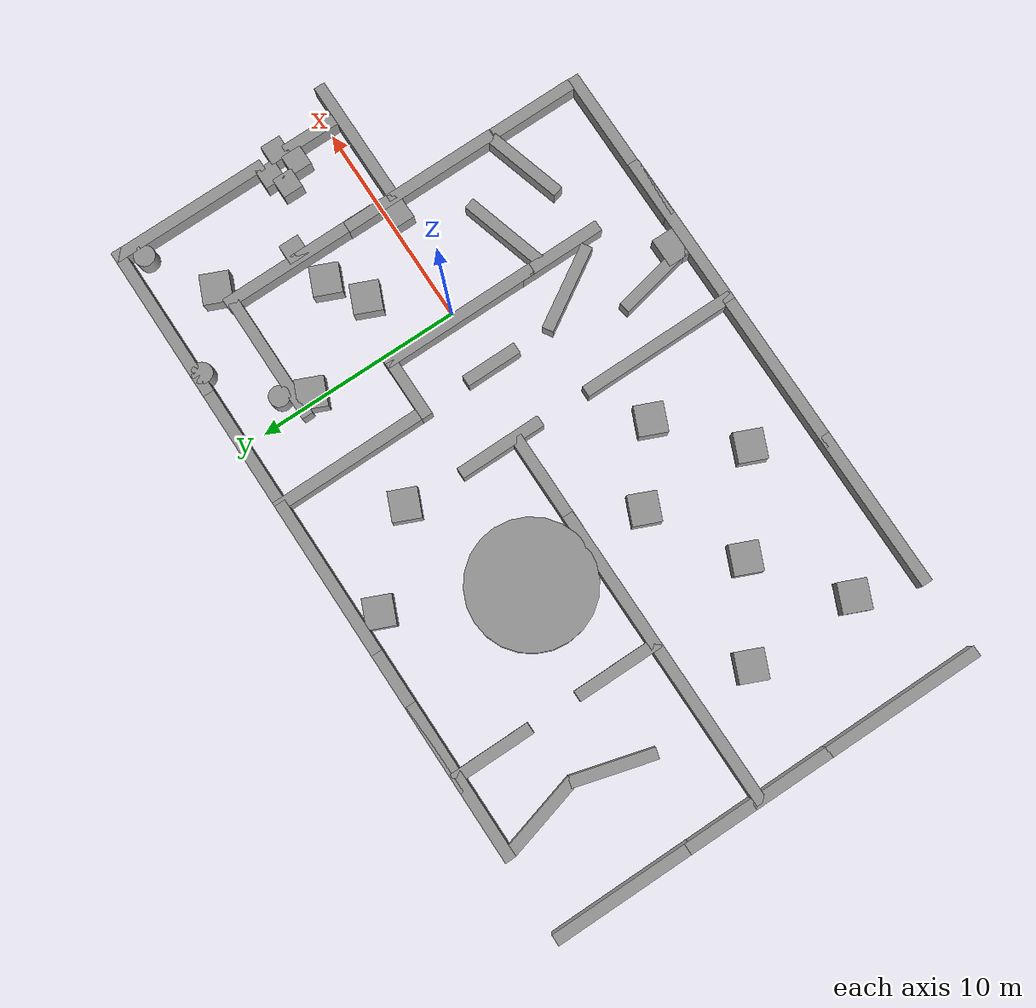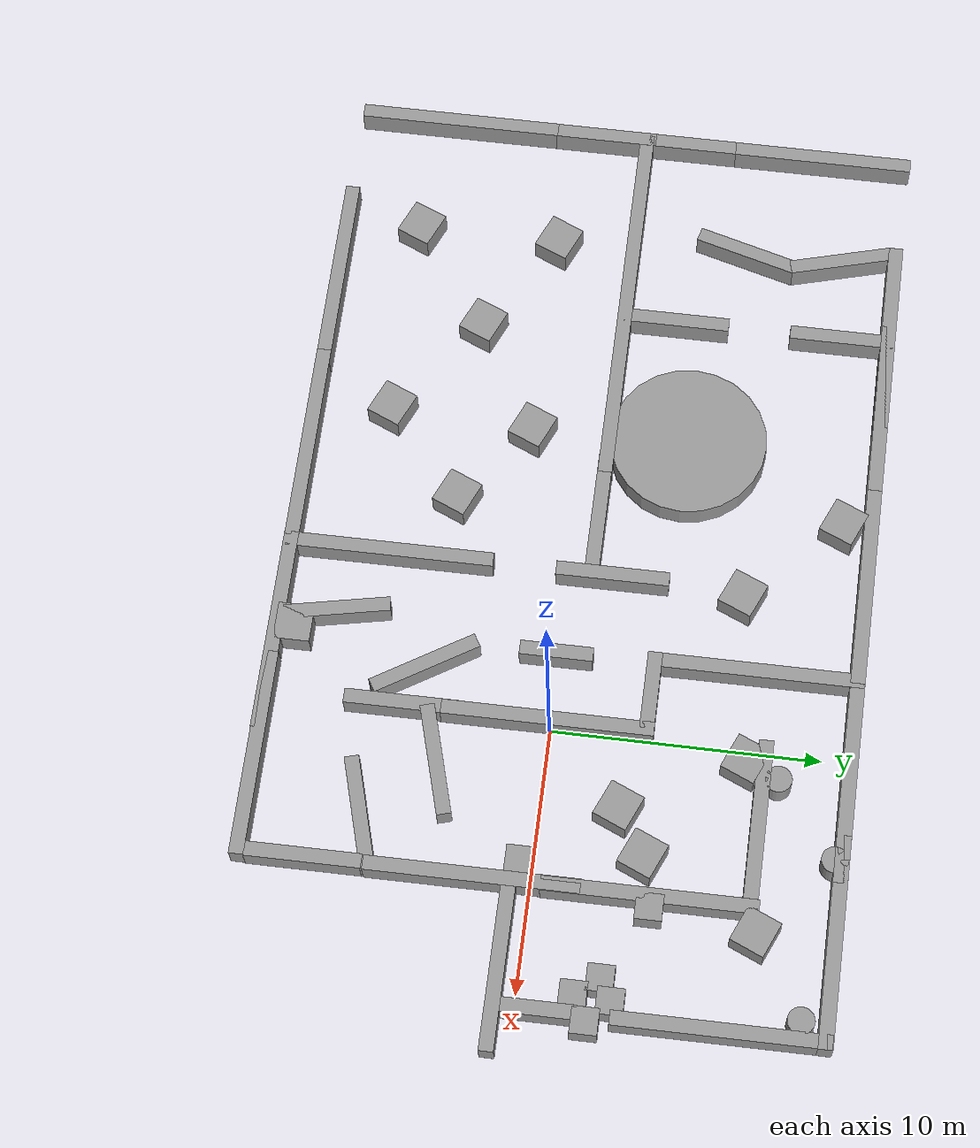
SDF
<?xml version='1.0'?>
<sdf version='1.6'>
  <model name='Maze01'>
    <link name='link_10'>
      <pose frame=''>9.80009 2.02423 9e-06 0 -0 0</pose>
      <inertial>
        <mass>1</mass>
        <inertia>
          <ixx>0.166667</ixx>
          <ixy>0</ixy>
          <ixz>0</ixz>
          <iyy>0.166667</iyy>
          <iyz>0</iyz>
          <izz>0.166667</izz>
        </inertia>
      </inertial>
      <visual name='visual'>
        <pose frame=''>0 0 0 0 -0 0</pose>
        <geometry>
          <box>
            <size>1 1 1</size>
          </box>
        </geometry>
        <material>
          <lighting>1</lighting>
          <script>
            <uri>file://media/materials/scripts/gazebo.material</uri>
            <name>Gazebo/Grey</name>
          </script>
          <ambient>0.3 0.3 0.3 1</ambient>
          <diffuse>0.7 0.7 0.7 1</diffuse>
          <specular>0.01 0.01 0.01 1</specular>
          <emissive>0 0 0 1</emissive>
        </material>
        <transparency>0</transparency>
        <cast_shadows>1</cast_shadows>
      </visual>
      <collision name='collision'>
        <laser_retro>0</laser_retro>
        <max_contacts>10</max_contacts>
        <pose frame=''>0 0 0 0 -0 0</pose>
        <geometry>
          <box>
            <size>1 1 1</size>
          </box>
        </geometry>
        <surface>
          <friction>
            <ode>
              <mu>1</mu>
              <mu2>1</mu2>
              <fdir1>0 0 0</fdir1>
              <slip1>0</slip1>
              <slip2>0</slip2>
            </ode>
            <torsional>
              <coefficient>1</coefficient>
              <patch_radius>0</patch_radius>
              <surface_radius>0</surface_radius>
              <use_patch_radius>1</use_patch_radius>
              <ode>
                <slip>0</slip>
              </ode>
            </torsional>
          </friction>
          <bounce>
            <restitution_coefficient>0</restitution_coefficient>
            <threshold>1e+06</threshold>
          </bounce>
          <contact>
            <collide_without_contact>0</collide_without_contact>
            <collide_without_contact_bitmask>1</collide_without_contact_bitmask>
            <collide_bitmask>1</collide_bitmask>
            <ode>
              <soft_cfm>0</soft_cfm>
              <soft_erp>0.2</soft_erp>
              <kp>1e+13</kp>
              <kd>1</kd>
              <max_vel>0.01</max_vel>
              <min_depth>0</min_depth>
            </ode>
            <bullet>
              <split_impulse>1</split_impulse>
              <split_impulse_penetration_threshold>-0.01</split_impulse_penetration_threshold>
              <soft_cfm>0</soft_cfm>
              <soft_erp>0.2</soft_erp>
              <kp>1e+13</kp>
              <kd>1</kd>
            </bullet>
          </contact>
        </surface>
      </collision>
    </link>
    <link name='link_11'>
      <pose frame=''>6.31823 4.34711 9e-06 0 -0 0</pose>
      <inertial>
        <mass>1</mass>
        <inertia>
          <ixx>0.166667</ixx>
          <ixy>0</ixy>
          <ixz>0</ixz>
          <iyy>0.166667</iyy>
          <iyz>0</iyz>
          <izz>0.166667</izz>
        </inertia>
      </inertial>
      <visual name='visual'>
        <pose frame=''>0 0 0 0 -0 0</pose>
        <geometry>
          <box>
            <size>1 1 1</size>
          </box>
        </geometry>
        <material>
          <lighting>1</lighting>
          <script>
            <uri>file://media/materials/scripts/gazebo.material</uri>
            <name>Gazebo/Grey</name>
          </script>
          <ambient>0.3 0.3 0.3 1</ambient>
          <diffuse>0.7 0.7 0.7 1</diffuse>
          <specular>0.01 0.01 0.01 1</specular>
          <emissive>0 0 0 1</emissive>
        </material>
        <transparency>0</transparency>
        <cast_shadows>1</cast_shadows>
      </visual>
      <collision name='collision'>
        <laser_retro>0</laser_retro>
        <max_contacts>10</max_contacts>
        <pose frame=''>0 0 0 0 -0 0</pose>
        <geometry>
          <box>
            <size>1 1 1</size>
          </box>
        </geometry>
        <surface>
          <friction>
            <ode>
              <mu>1</mu>
              <mu2>1</mu2>
              <fdir1>0 0 0</fdir1>
              <slip1>0</slip1>
              <slip2>0</slip2>
            </ode>
            <torsional>
              <coefficient>1</coefficient>
              <patch_radius>0</patch_radius>
              <surface_radius>0</surface_radius>
              <use_patch_radius>1</use_patch_radius>
              <ode>
                <slip>0</slip>
              </ode>
            </torsional>
          </friction>
          <bounce>
            <restitution_coefficient>0</restitution_coefficient>
            <threshold>1e+06</threshold>
          </bounce>
          <contact>
            <collide_without_contact>0</collide_without_contact>
            <collide_without_contact_bitmask>1</collide_without_contact_bitmask>
            <collide_bitmask>1</collide_bitmask>
            <ode>
              <soft_cfm>0</soft_cfm>
              <soft_erp>0.2</soft_erp>
              <kp>1e+13</kp>
              <kd>1</kd>
              <max_vel>0.01</max_vel>
              <min_depth>0</min_depth>
            </ode>
            <bullet>
              <split_impulse>1</split_impulse>
              <split_impulse_penetration_threshold>-0.01</split_impulse_penetration_threshold>
              <soft_cfm>0</soft_cfm>
              <soft_erp>0.2</soft_erp>
              <kp>1e+13</kp>
              <kd>1</kd>
            </bullet>
          </contact>
        </surface>
      </collision>
    </link>
    <link name='link_14'>
      <pose frame=''>10.7124 2.54643 9e-06 0 -0 0</pose>
      <inertial>
        <mass>1</mass>
        <inertia>
          <ixx>0.166667</ixx>
          <ixy>0</ixy>
          <ixz>0</ixz>
          <iyy>0.166667</iyy>
          <iyz>0</iyz>
          <izz>0.166667</izz>
        </inertia>
      </inertial>
      <visual name='visual'>
        <pose frame=''>0 0 0 0 -0 0</pose>
        <geometry>
          <box>
            <size>1 1 1</size>
          </box>
        </geometry>
        <material>
          <lighting>1</lighting>
          <script>
            <uri>file://media/materials/scripts/gazebo.material</uri>
            <name>Gazebo/Grey</name>
          </script>
          <ambient>0.3 0.3 0.3 1</ambient>
          <diffuse>0.7 0.7 0.7 1</diffuse>
          <specular>0.01 0.01 0.01 1</specular>
          <emissive>0 0 0 1</emissive>
        </material>
        <transparency>0</transparency>
        <cast_shadows>1</cast_shadows>
      </visual>
      <collision name='collision'>
        <laser_retro>0</laser_retro>
        <max_contacts>10</max_contacts>
        <pose frame=''>0 0 0 0 -0 0</pose>
        <geometry>
          <box>
            <size>1 1 1</size>
          </box>
        </geometry>
        <surface>
          <friction>
            <ode>
              <mu>1</mu>
              <mu2>1</mu2>
              <fdir1>0 0 0</fdir1>
              <slip1>0</slip1>
              <slip2>0</slip2>
            </ode>
            <torsional>
              <coefficient>1</coefficient>
              <patch_radius>0</patch_radius>
              <surface_radius>0</surface_radius>
              <use_patch_radius>1</use_patch_radius>
              <ode>
                <slip>0</slip>
              </ode>
            </torsional>
          </friction>
          <bounce>
            <restitution_coefficient>0</restitution_coefficient>
            <threshold>1e+06</threshold>
          </bounce>
          <contact>
            <collide_without_contact>0</collide_without_contact>
            <collide_without_contact_bitmask>1</collide_without_contact_bitmask>
            <collide_bitmask>1</collide_bitmask>
            <ode>
              <soft_cfm>0</soft_cfm>
              <soft_erp>0.2</soft_erp>
              <kp>1e+13</kp>
              <kd>1</kd>
              <max_vel>0.01</max_vel>
              <min_depth>0</min_depth>
            </ode>
            <bullet>
              <split_impulse>1</split_impulse>
              <split_impulse_penetration_threshold>-0.01</split_impulse_penetration_threshold>
              <soft_cfm>0</soft_cfm>
              <soft_erp>0.2</soft_erp>
              <kp>1e+13</kp>
              <kd>1</kd>
            </bullet>
          </contact>
        </surface>
      </collision>
    </link>

    <link name='link_4_clone_0_clone'>
      <pose frame=''>-17.8012 -10.6509 9e-06 0 -0 0</pose>
      <inertial>
        <mass>4.30693</mass>
        <inertia>
          <ixx>0.46587</ixx>
          <ixy>0</ixy>
          <ixz>0</ixz>
          <iyy>22.6991</iyy>
          <iyz>0</iyz>
          <izz>22.4471</izz>
        </inertia>
        <pose frame=''>0 0 0 0 -0 0</pose>
      </inertial>
      <visual name='visual'>
        <pose frame=''>0 0 0 0 -0 0</pose>
        <geometry>
          <box>
            <size>7.88951 0.545905 1</size>
          </box>
        </geometry>
        <material>
          <lighting>1</lighting>
          <script>
            <uri>file://media/materials/scripts/gazebo.material</uri>
            <name>Gazebo/Grey</name>
          </script>
          <ambient>0.3 0.3 0.3 1</ambient>
          <diffuse>0.7 0.7 0.7 1</diffuse>
          <specular>0.01 0.01 0.01 1</specular>
          <emissive>0 0 0 1</emissive>
          <shader type='pixel'/>
        </material>
        <transparency>0</transparency>
        <cast_shadows>1</cast_shadows>
      </visual>
      <collision name='collision'>
        <laser_retro>0</laser_retro>
        <max_contacts>10</max_contacts>
        <pose frame=''>0 0 0 0 -0 0</pose>
        <geometry>
          <box>
            <size>7.88951 0.545905 1</size>
          </box>
        </geometry>
        <surface>
          <friction>
            <ode>
              <mu>1</mu>
              <mu2>1</mu2>
              <fdir1>0 0 0</fdir1>
              <slip1>0</slip1>
              <slip2>0</slip2>
            </ode>
            <torsional>
              <coefficient>1</coefficient>
              <patch_radius>0</patch_radius>
              <surface_radius>0</surface_radius>
              <use_patch_radius>1</use_patch_radius>
              <ode>
                <slip>0</slip>
              </ode>
            </torsional>
          </friction>
          <bounce>
            <restitution_coefficient>0</restitution_coefficient>
            <threshold>1e+06</threshold>
          </bounce>
          <contact>
            <collide_without_contact>0</collide_without_contact>
            <collide_without_contact_bitmask>1</collide_without_contact_bitmask>
            <collide_bitmask>1</collide_bitmask>
            <ode>
              <soft_cfm>0</soft_cfm>
              <soft_erp>0.2</soft_erp>
              <kp>1e+13</kp>
              <kd>1</kd>
              <max_vel>0.01</max_vel>
              <min_depth>0</min_depth>
            </ode>
            <bullet>
              <split_impulse>1</split_impulse>
              <split_impulse_penetration_threshold>-0.01</split_impulse_penetration_threshold>
              <soft_cfm>0</soft_cfm>
              <soft_erp>0.2</soft_erp>
              <kp>1e+13</kp>
              <kd>1</kd>
            </bullet>
          </contact>
        </surface>
      </collision>
    </link>
    <link name='link_4_clone_0_clone_clone'>
      <pose frame=''>-17.57 11.05 9e-06 0 -0 0</pose>
      <inertial>
        <mass>4.30693</mass>
        <inertia>
          <ixx>0.46587</ixx>
          <ixy>0</ixy>
          <ixz>0</ixz>
          <iyy>22.6991</iyy>
          <iyz>0</iyz>
          <izz>22.4471</izz>
        </inertia>
        <pose frame=''>0 0 0 0 -0 0</pose>
      </inertial>
      <visual name='visual'>
        <pose frame=''>0 0 0 0 -0 0</pose>
        <geometry>
          <box>
            <size>7.88951 0.545905 1</size>
          </box>
        </geometry>
        <material>
          <lighting>1</lighting>
          <script>
            <uri>file://media/materials/scripts/gazebo.material</uri>
            <name>Gazebo/Grey</name>
          </script>
          <ambient>0.3 0.3 0.3 1</ambient>
          <diffuse>0.7 0.7 0.7 1</diffuse>
          <specular>0.01 0.01 0.01 1</specular>
          <emissive>0 0 0 1</emissive>
          <shader type='pixel'/>
        </material>
        <transparency>0</transparency>
        <cast_shadows>1</cast_shadows>
      </visual>
      <collision name='collision'>
        <laser_retro>0</laser_retro>
        <max_contacts>10</max_contacts>
        <pose frame=''>0 0 0 0 -0 0</pose>
        <geometry>
          <box>
            <size>7.88951 0.545905 1</size>
          </box>
        </geometry>
        <surface>
          <friction>
            <ode>
              <mu>1</mu>
              <mu2>1</mu2>
              <fdir1>0 0 0</fdir1>
              <slip1>0</slip1>
              <slip2>0</slip2>
            </ode>
            <torsional>
              <coefficient>1</coefficient>
              <patch_radius>0</patch_radius>
              <surface_radius>0</surface_radius>
              <use_patch_radius>1</use_patch_radius>
              <ode>
                <slip>0</slip>
              </ode>
            </torsional>
          </friction>
          <bounce>
            <restitution_coefficient>0</restitution_coefficient>
            <threshold>1e+06</threshold>
          </bounce>
          <contact>
            <collide_without_contact>0</collide_without_contact>
            <collide_without_contact_bitmask>1</collide_without_contact_bitmask>
            <collide_bitmask>1</collide_bitmask>
            <ode>
              <soft_cfm>0</soft_cfm>
              <soft_erp>0.2</soft_erp>
              <kp>1e+13</kp>
              <kd>1</kd>
              <max_vel>0.01</max_vel>
              <min_depth>0</min_depth>
            </ode>
            <bullet>
              <split_impulse>1</split_impulse>
              <split_impulse_penetration_threshold>-0.01</split_impulse_penetration_threshold>
              <soft_cfm>0</soft_cfm>
              <soft_erp>0.2</soft_erp>
              <kp>1e+13</kp>
              <kd>1</kd>
            </bullet>
          </contact>
        </surface>
      </collision>
    </link>
    <link name='link_4_clone_0_clone_clone_0'>
      <pose frame=''>-14.0594 11.05 9e-06 0 -0 0</pose>
      <inertial>
        <mass>4.30693</mass>
        <inertia>
          <ixx>0.46587</ixx>
          <ixy>0</ixy>
          <ixz>0</ixz>
          <iyy>22.6991</iyy>
          <iyz>0</iyz>
          <izz>22.4471</izz>
        </inertia>
        <pose frame=''>0 0 0 0 -0 0</pose>
      </inertial>
      <visual name='visual'>
        <pose frame=''>0 0 0 0 -0 0</pose>
        <geometry>
          <box>
            <size>7.88951 0.545905 1</size>
          </box>
        </geometry>
        <material>
          <lighting>1</lighting>
          <script>
            <uri>file://media/materials/scripts/gazebo.material</uri>
            <name>Gazebo/Grey</name>
          </script>
          <ambient>0.3 0.3 0.3 1</ambient>
          <diffuse>0.7 0.7 0.7 1</diffuse>
          <specular>0.01 0.01 0.01 1</specular>
          <emissive>0 0 0 1</emissive>
          <shader type='pixel'/>
        </material>
        <transparency>0</transparency>
        <cast_shadows>1</cast_shadows>
      </visual>
      <collision name='collision'>
        <laser_retro>0</laser_retro>
        <max_contacts>10</max_contacts>
        <pose frame=''>0 0 0 0 -0 0</pose>
        <geometry>
          <box>
            <size>7.88951 0.545905 1</size>
          </box>
        </geometry>
        <surface>
          <friction>
            <ode>
              <mu>1</mu>
              <mu2>1</mu2>
              <fdir1>0 0 0</fdir1>
              <slip1>0</slip1>
              <slip2>0</slip2>
            </ode>
            <torsional>
              <coefficient>1</coefficient>
              <patch_radius>0</patch_radius>
              <surface_radius>0</surface_radius>
              <use_patch_radius>1</use_patch_radius>
              <ode>
                <slip>0</slip>
              </ode>
            </torsional>
          </friction>
          <bounce>
            <restitution_coefficient>0</restitution_coefficient>
            <threshold>1e+06</threshold>
          </bounce>
          <contact>
            <collide_without_contact>0</collide_without_contact>
            <collide_without_contact_bitmask>1</collide_without_contact_bitmask>
            <collide_bitmask>1</collide_bitmask>
            <ode>
              <soft_cfm>0</soft_cfm>
              <soft_erp>0.2</soft_erp>
              <kp>1e+13</kp>
              <kd>1</kd>
              <max_vel>0.01</max_vel>
              <min_depth>0</min_depth>
            </ode>
            <bullet>
              <split_impulse>1</split_impulse>
              <split_impulse_penetration_threshold>-0.01</split_impulse_penetration_threshold>
              <soft_cfm>0</soft_cfm>
              <soft_erp>0.2</soft_erp>
              <kp>1e+13</kp>
              <kd>1</kd>
            </bullet>
          </contact>
        </surface>
      </collision>
    </link>
    <link name='link_4_clone_0_clone_clone_1'>
      <pose frame=''>-10.458 -10.6545 9e-06 0 -0 0</pose>
      <inertial>
        <mass>4.30693</mass>
        <inertia>
          <ixx>0.46587</ixx>
          <ixy>0</ixy>
          <ixz>0</ixz>
          <iyy>22.6991</iyy>
          <iyz>0</iyz>
          <izz>22.4471</izz>
        </inertia>
        <pose frame=''>0 0 0 0 -0 0</pose>
      </inertial>
      <visual name='visual'>
        <pose frame=''>0 0 0 0 -0 0</pose>
        <geometry>
          <box>
            <size>7.88951 0.545905 1</size>
          </box>
        </geometry>
        <material>
          <lighting>1</lighting>
          <script>
            <uri>file://media/materials/scripts/gazebo.material</uri>
            <name>Gazebo/Grey</name>
          </script>
          <ambient>0.3 0.3 0.3 1</ambient>
          <diffuse>0.7 0.7 0.7 1</diffuse>
          <specular>0.01 0.01 0.01 1</specular>
          <emissive>0 0 0 1</emissive>
          <shader type='pixel'/>
        </material>
        <transparency>0</transparency>
        <cast_shadows>1</cast_shadows>
      </visual>
      <collision name='collision'>
        <laser_retro>0</laser_retro>
        <max_contacts>10</max_contacts>
        <pose frame=''>0 0 0 0 -0 0</pose>
        <geometry>
          <box>
            <size>7.88951 0.545905 1</size>
          </box>
        </geometry>
        <surface>
          <friction>
            <ode>
              <mu>1</mu>
              <mu2>1</mu2>
              <fdir1>0 0 0</fdir1>
              <slip1>0</slip1>
              <slip2>0</slip2>
            </ode>
            <torsional>
              <coefficient>1</coefficient>
              <patch_radius>0</patch_radius>
              <surface_radius>0</surface_radius>
              <use_patch_radius>1</use_patch_radius>
              <ode>
                <slip>0</slip>
              </ode>
            </torsional>
          </friction>
          <bounce>
            <restitution_coefficient>0</restitution_coefficient>
            <threshold>1e+06</threshold>
          </bounce>
          <contact>
            <collide_without_contact>0</collide_without_contact>
            <collide_without_contact_bitmask>1</collide_without_contact_bitmask>
            <collide_bitmask>1</collide_bitmask>
            <ode>
              <soft_cfm>0</soft_cfm>
              <soft_erp>0.2</soft_erp>
              <kp>1e+13</kp>
              <kd>1</kd>
              <max_vel>0.01</max_vel>
              <min_depth>0</min_depth>
            </ode>
            <bullet>
              <split_impulse>1</split_impulse>
              <split_impulse_penetration_threshold>-0.01</split_impulse_penetration_threshold>
              <soft_cfm>0</soft_cfm>
              <soft_erp>0.2</soft_erp>
              <kp>1e+13</kp>
              <kd>1</kd>
            </bullet>
          </contact>
        </surface>
      </collision>
    </link>
    <link name='link_4_clone_0_clone_clone_1_clone_0'>
      <pose frame=''>-2.67814 -10.6624 9e-06 0 -0 0</pose>
      <inertial>
        <mass>4.30693</mass>
        <inertia>
          <ixx>0.46587</ixx>
          <ixy>0</ixy>
          <ixz>0</ixz>
          <iyy>22.6991</iyy>
          <iyz>0</iyz>
          <izz>22.4471</izz>
        </inertia>
        <pose frame=''>0 0 0 0 -0 0</pose>
      </inertial>
      <visual name='visual'>
        <pose frame=''>0 0 0 0 -0 0</pose>
        <geometry>
          <box>
            <size>7.88951 0.545905 1</size>
          </box>
        </geometry>
        <material>
          <lighting>1</lighting>
          <script>
            <uri>file://media/materials/scripts/gazebo.material</uri>
            <name>Gazebo/Grey</name>
          </script>
          <ambient>0.3 0.3 0.3 1</ambient>
          <diffuse>0.7 0.7 0.7 1</diffuse>
          <specular>0.01 0.01 0.01 1</specular>
          <emissive>0 0 0 1</emissive>
          <shader type='pixel'/>
        </material>
        <transparency>0</transparency>
        <cast_shadows>1</cast_shadows>
      </visual>
      <collision name='collision'>
        <laser_retro>0</laser_retro>
        <max_contacts>10</max_contacts>
        <pose frame=''>0 0 0 0 -0 0</pose>
        <geometry>
          <box>
            <size>7.88951 0.545905 1</size>
          </box>
        </geometry>
        <surface>
          <friction>
            <ode>
              <mu>1</mu>
              <mu2>1</mu2>
              <fdir1>0 0 0</fdir1>
              <slip1>0</slip1>
              <slip2>0</slip2>
            </ode>
            <torsional>
              <coefficient>1</coefficient>
              <patch_radius>0</patch_radius>
              <surface_radius>0</surface_radius>
              <use_patch_radius>1</use_patch_radius>
              <ode>
                <slip>0</slip>
              </ode>
            </torsional>
          </friction>
          <bounce>
            <restitution_coefficient>0</restitution_coefficient>
            <threshold>1e+06</threshold>
          </bounce>
          <contact>
            <collide_without_contact>0</collide_without_contact>
            <collide_without_contact_bitmask>1</collide_without_contact_bitmask>
            <collide_bitmask>1</collide_bitmask>
            <ode>
              <soft_cfm>0</soft_cfm>
              <soft_erp>0.2</soft_erp>
              <kp>1e+13</kp>
              <kd>1</kd>
              <max_vel>0.01</max_vel>
              <min_depth>0</min_depth>
            </ode>
            <bullet>
              <split_impulse>1</split_impulse>
              <split_impulse_penetration_threshold>-0.01</split_impulse_penetration_threshold>
              <soft_cfm>0</soft_cfm>
              <soft_erp>0.2</soft_erp>
              <kp>1e+13</kp>
              <kd>1</kd>
            </bullet>
          </contact>
        </surface>
      </collision>
    </link>
    <link name='link_4_clone_0_clone_clone_1_clone_0_clone'>
      <pose frame=''>2.19804 -10.643 9e-06 0 -0 0</pose>
      <inertial>
        <mass>4.30693</mass>
        <inertia>
          <ixx>0.46587</ixx>
          <ixy>0</ixy>
          <ixz>0</ixz>
          <iyy>22.6991</iyy>
          <iyz>0</iyz>
          <izz>22.4471</izz>
        </inertia>
        <pose frame=''>0 0 0 0 -0 0</pose>
      </inertial>
      <visual name='visual'>
        <pose frame=''>0 0 0 0 -0 0</pose>
        <geometry>
          <box>
            <size>7.88951 0.545905 1</size>
          </box>
        </geometry>
        <material>
          <lighting>1</lighting>
          <script>
            <uri>file://media/materials/scripts/gazebo.material</uri>
            <name>Gazebo/Grey</name>
          </script>
          <ambient>0.3 0.3 0.3 1</ambient>
          <diffuse>0.7 0.7 0.7 1</diffuse>
          <specular>0.01 0.01 0.01 1</specular>
          <emissive>0 0 0 1</emissive>
          <shader type='pixel'/>
        </material>
        <transparency>0</transparency>
        <cast_shadows>1</cast_shadows>
      </visual>
      <collision name='collision'>
        <laser_retro>0</laser_retro>
        <max_contacts>10</max_contacts>
        <pose frame=''>0 0 0 0 -0 0</pose>
        <geometry>
          <box>
            <size>7.88951 0.545905 1</size>
          </box>
        </geometry>
        <surface>
          <friction>
            <ode>
              <mu>1</mu>
              <mu2>1</mu2>
              <fdir1>0 0 0</fdir1>
              <slip1>0</slip1>
              <slip2>0</slip2>
            </ode>
            <torsional>
              <coefficient>1</coefficient>
              <patch_radius>0</patch_radius>
              <surface_radius>0</surface_radius>
              <use_patch_radius>1</use_patch_radius>
              <ode>
                <slip>0</slip>
              </ode>
            </torsional>
          </friction>
          <bounce>
            <restitution_coefficient>0</restitution_coefficient>
            <threshold>1e+06</threshold>
          </bounce>
          <contact>
            <collide_without_contact>0</collide_without_contact>
            <collide_without_contact_bitmask>1</collide_without_contact_bitmask>
            <collide_bitmask>1</collide_bitmask>
            <ode>
              <soft_cfm>0</soft_cfm>
              <soft_erp>0.2</soft_erp>
              <kp>1e+13</kp>
              <kd>1</kd>
              <max_vel>0.01</max_vel>
              <min_depth>0</min_depth>
            </ode>
            <bullet>
              <split_impulse>1</split_impulse>
              <split_impulse_penetration_threshold>-0.01</split_impulse_penetration_threshold>
              <soft_cfm>0</soft_cfm>
              <soft_erp>0.2</soft_erp>
              <kp>1e+13</kp>
              <kd>1</kd>
            </bullet>
          </contact>
        </surface>
      </collision>
    </link>
    <link name='link_4_clone_0_clone_clone_1_clone_0_clone_0'>
      <pose frame=''>0.695253 11.0512 9e-06 0 -0 0</pose>
      <inertial>
        <mass>4.30693</mass>
        <inertia>
          <ixx>0.46587</ixx>
          <ixy>0</ixy>
          <ixz>0</ixz>
          <iyy>22.6991</iyy>
          <iyz>0</iyz>
          <izz>22.4471</izz>
        </inertia>
        <pose frame=''>0 0 0 0 -0 0</pose>
      </inertial>
      <visual name='visual'>
        <pose frame=''>0 0 0 0 -0 0</pose>
        <geometry>
          <box>
            <size>7.88951 0.545905 1</size>
          </box>
        </geometry>
        <material>
          <lighting>1</lighting>
          <script>
            <uri>file://media/materials/scripts/gazebo.material</uri>
            <name>Gazebo/Grey</name>
          </script>
          <ambient>0.3 0.3 0.3 1</ambient>
          <diffuse>0.7 0.7 0.7 1</diffuse>
          <specular>0.01 0.01 0.01 1</specular>
          <emissive>0 0 0 1</emissive>
          <shader type='pixel'/>
        </material>
        <transparency>0</transparency>
        <cast_shadows>1</cast_shadows>
      </visual>
      <collision name='collision'>
        <laser_retro>0</laser_retro>
        <max_contacts>10</max_contacts>
        <pose frame=''>0 0 0 0 -0 0</pose>
        <geometry>
          <box>
            <size>7.88951 0.545905 1</size>
          </box>
        </geometry>
        <surface>
          <friction>
            <ode>
              <mu>1</mu>
              <mu2>1</mu2>
              <fdir1>0 0 0</fdir1>
              <slip1>0</slip1>
              <slip2>0</slip2>
            </ode>
            <torsional>
              <coefficient>1</coefficient>
              <patch_radius>0</patch_radius>
              <surface_radius>0</surface_radius>
              <use_patch_radius>1</use_patch_radius>
              <ode>
                <slip>0</slip>
              </ode>
            </torsional>
          </friction>
          <bounce>
            <restitution_coefficient>0</restitution_coefficient>
            <threshold>1e+06</threshold>
          </bounce>
          <contact>
            <collide_without_contact>0</collide_without_contact>
            <collide_without_contact_bitmask>1</collide_without_contact_bitmask>
            <collide_bitmask>1</collide_bitmask>
            <ode>
              <soft_cfm>0</soft_cfm>
              <soft_erp>0.2</soft_erp>
              <kp>1e+13</kp>
              <kd>1</kd>
              <max_vel>0.01</max_vel>
              <min_depth>0</min_depth>
            </ode>
            <bullet>
              <split_impulse>1</split_impulse>
              <split_impulse_penetration_threshold>-0.01</split_impulse_penetration_threshold>
              <soft_cfm>0</soft_cfm>
              <soft_erp>0.2</soft_erp>
              <kp>1e+13</kp>
              <kd>1</kd>
            </bullet>
          </contact>
        </surface>
      </collision>
    </link>
    <link name='partition_8'>
      <pose frame=''>-7.0 11.0512 9e-06 0 -0 0</pose>
      <inertial>
        <mass>4.30693</mass>
        <inertia>
          <ixx>0.46587</ixx>
          <ixy>0</ixy>
          <ixz>0</ixz>
          <iyy>22.6991</iyy>
          <iyz>0</iyz>
          <izz>22.4471</izz>
        </inertia>
        <pose frame=''>0 0 0 0 -0 0</pose>
      </inertial>
      <visual name='visual'>
        <pose frame=''>0 0 0 0 -0 0</pose>
        <geometry>
          <box>
            <size>7.88951 0.545905 1</size>
          </box>
        </geometry>
        <material>
          <lighting>1</lighting>
          <script>
            <uri>file://media/materials/scripts/gazebo.material</uri>
            <name>Gazebo/Grey</name>
          </script>
          <ambient>0.3 0.3 0.3 1</ambient>
          <diffuse>0.7 0.7 0.7 1</diffuse>
          <specular>0.01 0.01 0.01 1</specular>
          <emissive>0 0 0 1</emissive>
          <shader type='pixel'/>
        </material>
        <transparency>0</transparency>
        <cast_shadows>1</cast_shadows>
      </visual>
      <collision name='collision'>
        <laser_retro>0</laser_retro>
        <max_contacts>10</max_contacts>
        <pose frame=''>0 0 0 0 -0 0</pose>
        <geometry>
          <box>
            <size>7.88951 0.545905 1</size>
          </box>
        </geometry>
        <surface>
          <friction>
            <ode>
              <mu>1</mu>
              <mu2>1</mu2>
              <fdir1>0 0 0</fdir1>
              <slip1>0</slip1>
              <slip2>0</slip2>
            </ode>
            <torsional>
              <coefficient>1</coefficient>
              <patch_radius>0</patch_radius>
              <surface_radius>0</surface_radius>
              <use_patch_radius>1</use_patch_radius>
              <ode>
                <slip>0</slip>
              </ode>
            </torsional>
          </friction>
          <bounce>
            <restitution_coefficient>0</restitution_coefficient>
            <threshold>1e+06</threshold>
          </bounce>
          <contact>
            <collide_without_contact>0</collide_without_contact>
            <collide_without_contact_bitmask>1</collide_without_contact_bitmask>
            <collide_bitmask>1</collide_bitmask>
            <ode>
              <soft_cfm>0</soft_cfm>
              <soft_erp>0.2</soft_erp>
              <kp>1e+13</kp>
              <kd>1</kd>
              <max_vel>0.01</max_vel>
              <min_depth>0</min_depth>
            </ode>
            <bullet>
              <split_impulse>1</split_impulse>
              <split_impulse_penetration_threshold>-0.01</split_impulse_penetration_threshold>
              <soft_cfm>0</soft_cfm>
              <soft_erp>0.2</soft_erp>
              <kp>1e+13</kp>
              <kd>1</kd>
            </bullet>
          </contact>
        </surface>
      </collision>
    </link>
    <link name='link_4_clone_0_clone_clone_1_clone_0_clone_0_clone'>
      <pose frame=''>6.79233 11.05 9e-06 0 -0 0</pose>
      <inertial>
        <mass>4.30693</mass>
        <inertia>
          <ixx>0.46587</ixx>
          <ixy>0</ixy>
          <ixz>0</ixz>
          <iyy>22.6991</iyy>
          <iyz>0</iyz>
          <izz>22.4471</izz>
        </inertia>
        <pose frame=''>0 0 0 0 -0 0</pose>
      </inertial>
      <visual name='visual'>
        <pose frame=''>0 0 0 0 -0 0</pose>
        <geometry>
          <box>
            <size>7.88951 0.545905 1</size>
          </box>
        </geometry>
        <material>
          <lighting>1</lighting>
          <script>
            <uri>file://media/materials/scripts/gazebo.material</uri>
            <name>Gazebo/Grey</name>
          </script>
          <ambient>0.3 0.3 0.3 1</ambient>
          <diffuse>0.7 0.7 0.7 1</diffuse>
          <specular>0.01 0.01 0.01 1</specular>
          <emissive>0 0 0 1</emissive>
          <shader type='pixel'/>
        </material>
        <transparency>0</transparency>
        <cast_shadows>1</cast_shadows>
      </visual>
      <collision name='collision'>
        <laser_retro>0</laser_retro>
        <max_contacts>10</max_contacts>
        <pose frame=''>0 0 0 0 -0 0</pose>
        <geometry>
          <box>
            <size>7.88951 0.545905 1</size>
          </box>
        </geometry>
        <surface>
          <friction>
            <ode>
              <mu>1</mu>
              <mu2>1</mu2>
              <fdir1>0 0 0</fdir1>
              <slip1>0</slip1>
              <slip2>0</slip2>
            </ode>
            <torsional>
              <coefficient>1</coefficient>
              <patch_radius>0</patch_radius>
              <surface_radius>0</surface_radius>
              <use_patch_radius>1</use_patch_radius>
              <ode>
                <slip>0</slip>
              </ode>
            </torsional>
          </friction>
          <bounce>
            <restitution_coefficient>0</restitution_coefficient>
            <threshold>1e+06</threshold>
          </bounce>
          <contact>
            <collide_without_contact>0</collide_without_contact>
            <collide_without_contact_bitmask>1</collide_without_contact_bitmask>
            <collide_bitmask>1</collide_bitmask>
            <ode>
              <soft_cfm>0</soft_cfm>
              <soft_erp>0.2</soft_erp>
              <kp>1e+13</kp>
              <kd>1</kd>
              <max_vel>0.01</max_vel>
              <min_depth>0</min_depth>
            </ode>
            <bullet>
              <split_impulse>1</split_impulse>
              <split_impulse_penetration_threshold>-0.01</split_impulse_penetration_threshold>
              <soft_cfm>0</soft_cfm>
              <soft_erp>0.2</soft_erp>
              <kp>1e+13</kp>
              <kd>1</kd>
            </bullet>
          </contact>
        </surface>
      </collision>
    </link>

    <link name='link_4_clone_0_clone_clone_1_clone_clone'>
      <pose frame=''>2.76705 7.92871 9e-06 0 -0 0</pose>
      <inertial>
        <mass>3.50538</mass>
        <inertia>
          <ixx>0.379168</ixx>
          <ixy>0</ixy>
          <ixz>0</ixz>
          <iyy>12.3366</iyy>
          <iyz>0</iyz>
          <izz>12.1315</izz>
        </inertia>
        <pose frame=''>0 0 0 0 -0 0</pose>
      </inertial>
      <visual name='visual'>
        <pose frame=''>0 0 0 0 -0 0</pose>
        <geometry>
          <box>
            <size>6.42122 0.545905 1</size>
          </box>
        </geometry>
        <material>
          <lighting>1</lighting>
          <script>
            <uri>file://media/materials/scripts/gazebo.material</uri>
            <name>Gazebo/Grey</name>
          </script>
          <ambient>0.3 0.3 0.3 1</ambient>
          <diffuse>0.7 0.7 0.7 1</diffuse>
          <specular>0.01 0.01 0.01 1</specular>
          <emissive>0 0 0 1</emissive>
          <shader type='pixel'/>
        </material>
        <transparency>0</transparency>
        <cast_shadows>1</cast_shadows>
      </visual>
      <collision name='collision'>
        <laser_retro>0</laser_retro>
        <max_contacts>10</max_contacts>
        <pose frame=''>0 0 0 0 -0 0</pose>
        <geometry>
          <box>
            <size>6.42122 0.545905 1</size>
          </box>
        </geometry>
        <surface>
          <friction>
            <ode>
              <mu>1</mu>
              <mu2>1</mu2>
              <fdir1>0 0 0</fdir1>
              <slip1>0</slip1>
              <slip2>0</slip2>
            </ode>
            <torsional>
              <coefficient>1</coefficient>
              <patch_radius>0</patch_radius>
              <surface_radius>0</surface_radius>
              <use_patch_radius>1</use_patch_radius>
              <ode>
                <slip>0</slip>
              </ode>
            </torsional>
          </friction>
          <bounce>
            <restitution_coefficient>0</restitution_coefficient>
            <threshold>1e+06</threshold>
          </bounce>
          <contact>
            <collide_without_contact>0</collide_without_contact>
            <collide_without_contact_bitmask>1</collide_without_contact_bitmask>
            <collide_bitmask>1</collide_bitmask>
            <ode>
              <soft_cfm>0</soft_cfm>
              <soft_erp>0.2</soft_erp>
              <kp>1e+13</kp>
              <kd>1</kd>
              <max_vel>0.01</max_vel>
              <min_depth>0</min_depth>
            </ode>
            <bullet>
              <split_impulse>1</split_impulse>
              <split_impulse_penetration_threshold>-0.01</split_impulse_penetration_threshold>
              <soft_cfm>0</soft_cfm>
              <soft_erp>0.2</soft_erp>
              <kp>1e+13</kp>
              <kd>1</kd>
            </bullet>
          </contact>
        </surface>
      </collision>
    </link>

    <link name='robot3_block'>
      <pose frame=''>9 -0.75 9e-06 0 -0 0</pose>
      <inertial>
        <mass>3.50538</mass>
        <inertia>
          <ixx>0.379168</ixx>
          <ixy>0</ixy>
          <ixz>0</ixz>
          <iyy>12.3366</iyy>
          <iyz>0</iyz>
          <izz>12.1315</izz>
        </inertia>
        <pose frame=''>0 0 0 0 -0 0</pose>
      </inertial>
      <visual name='visual'>
        <pose frame=''>0 0 0 0 -0 0</pose>
        <geometry>
          <box>
            <size>6.42122 0.545905 1</size>
          </box>
        </geometry>
        <material>
          <lighting>1</lighting>
          <script>
            <uri>file://media/materials/scripts/gazebo.material</uri>
            <name>Gazebo/Grey</name>
          </script>
          <ambient>0.3 0.3 0.3 1</ambient>
          <diffuse>0.7 0.7 0.7 1</diffuse>
          <specular>0.01 0.01 0.01 1</specular>
          <emissive>0 0 0 1</emissive>
          <shader type='pixel'/>
        </material>
        <transparency>0</transparency>
        <cast_shadows>1</cast_shadows>
      </visual>
      <collision name='collision'>
        <laser_retro>0</laser_retro>
        <max_contacts>10</max_contacts>
        <pose frame=''>0 0 0 0 -0 0</pose>
        <geometry>
          <box>
            <size>6.42122 0.545905 1</size>
          </box>
        </geometry>
        <surface>
          <friction>
            <ode>
              <mu>1</mu>
              <mu2>1</mu2>
              <fdir1>0 0 0</fdir1>
              <slip1>0</slip1>
              <slip2>0</slip2>
            </ode>
            <torsional>
              <coefficient>1</coefficient>
              <patch_radius>0</patch_radius>
              <surface_radius>0</surface_radius>
              <use_patch_radius>1</use_patch_radius>
              <ode>
                <slip>0</slip>
              </ode>
            </torsional>
          </friction>
          <bounce>
            <restitution_coefficient>0</restitution_coefficient>
            <threshold>1e+06</threshold>
          </bounce>
          <contact>
            <collide_without_contact>0</collide_without_contact>
            <collide_without_contact_bitmask>1</collide_without_contact_bitmask>
            <collide_bitmask>1</collide_bitmask>
            <ode>
              <soft_cfm>0</soft_cfm>
              <soft_erp>0.2</soft_erp>
              <kp>1e+13</kp>
              <kd>1</kd>
              <max_vel>0.01</max_vel>
              <min_depth>0</min_depth>
            </ode>
            <bullet>
              <split_impulse>1</split_impulse>
              <split_impulse_penetration_threshold>-0.01</split_impulse_penetration_threshold>
              <soft_cfm>0</soft_cfm>
              <soft_erp>0.2</soft_erp>
              <kp>1e+13</kp>
              <kd>1</kd>
            </bullet>
          </contact>
        </surface>
      </collision>
    </link>

    <link name='new_wall'>
      <pose frame=''>-1.9 3.51 9e-06 0 -0 0</pose>
      <inertial>
        <mass>3.50538</mass>
        <inertia>
          <ixx>0.379168</ixx>
          <ixy>0</ixy>
          <ixz>0</ixz>
          <iyy>12.3366</iyy>
          <iyz>0</iyz>
          <izz>12.1315</izz>
        </inertia>
        <pose frame=''>0 0 0 0 -0 0</pose>
      </inertial>
      <visual name='visual'>
        <pose frame=''>0 0 0 0 -0 0</pose>
        <geometry>
          <box>
            <size>3 0.545905 1</size>
          </box>
        </geometry>
        <material>
          <lighting>1</lighting>
          <script>
            <uri>file://media/materials/scripts/gazebo.material</uri>
            <name>Gazebo/Grey</name>
          </script>
          <ambient>0.3 0.3 0.3 1</ambient>
          <diffuse>0.7 0.7 0.7 1</diffuse>
          <specular>0.01 0.01 0.01 1</specular>
          <emissive>0 0 0 1</emissive>
          <shader type='pixel'/>
        </material>
        <transparency>0</transparency>
        <cast_shadows>1</cast_shadows>
      </visual>
      <collision name='collision'>
        <laser_retro>0</laser_retro>
        <max_contacts>10</max_contacts>
        <pose frame=''>0 0 0 0 -0 0</pose>
        <geometry>
          <box>
            <size>3 0.545905 1</size>
          </box>
        </geometry>
        <surface>
          <friction>
            <ode>
              <mu>1</mu>
              <mu2>1</mu2>
              <fdir1>0 0 0</fdir1>
              <slip1>0</slip1>
              <slip2>0</slip2>
            </ode>
            <torsional>
              <coefficient>1</coefficient>
              <patch_radius>0</patch_radius>
              <surface_radius>0</surface_radius>
              <use_patch_radius>1</use_patch_radius>
              <ode>
                <slip>0</slip>
              </ode>
            </torsional>
          </friction>
          <bounce>
            <restitution_coefficient>0</restitution_coefficient>
            <threshold>1e+06</threshold>
          </bounce>
          <contact>
            <collide_without_contact>0</collide_without_contact>
            <collide_without_contact_bitmask>1</collide_without_contact_bitmask>
            <collide_bitmask>1</collide_bitmask>
            <ode>
              <soft_cfm>0</soft_cfm>
              <soft_erp>0.2</soft_erp>
              <kp>1e+13</kp>
              <kd>1</kd>
              <max_vel>0.01</max_vel>
              <min_depth>0</min_depth>
            </ode>
            <bullet>
              <split_impulse>1</split_impulse>
              <split_impulse_penetration_threshold>-0.01</split_impulse_penetration_threshold>
              <soft_cfm>0</soft_cfm>
              <soft_erp>0.2</soft_erp>
              <kp>1e+13</kp>
              <kd>1</kd>
            </bullet>
          </contact>
        </surface>
      </collision>
    </link>

    <link name='new_wall_2'>
      <pose frame=''>-8.87 0.76 9e-06 0 -0 0</pose>
      <inertial>
        <mass>3.50538</mass>
        <inertia>
          <ixx>0.379168</ixx>
          <ixy>0</ixy>
          <ixz>0</ixz>
          <iyy>12.3366</iyy>
          <iyz>0</iyz>
          <izz>12.1315</izz>
        </inertia>
        <pose frame=''>0 0 0 0 -0 0</pose>
      </inertial>
      <visual name='visual'>
        <pose frame=''>0 0 0 0 -0 0</pose>
        <geometry>
          <box>
            <size>5 0.545905 1</size>
          </box>
        </geometry>
        <material>
          <lighting>1</lighting>
          <script>
            <uri>file://media/materials/scripts/gazebo.material</uri>
            <name>Gazebo/Grey</name>
          </script>
          <ambient>0.3 0.3 0.3 1</ambient>
          <diffuse>0.7 0.7 0.7 1</diffuse>
          <specular>0.01 0.01 0.01 1</specular>
          <emissive>0 0 0 1</emissive>
          <shader type='pixel'/>
        </material>
        <transparency>0</transparency>
        <cast_shadows>1</cast_shadows>
      </visual>
      <collision name='collision'>
        <laser_retro>0</laser_retro>
        <max_contacts>10</max_contacts>
        <pose frame=''>0 0 0 0 -0 0</pose>
        <geometry>
          <box>
            <size>5 0.545905 1</size>
          </box>
        </geometry>
        <surface>
          <friction>
            <ode>
              <mu>1</mu>
              <mu2>1</mu2>
              <fdir1>0 0 0</fdir1>
              <slip1>0</slip1>
              <slip2>0</slip2>
            </ode>
            <torsional>
              <coefficient>1</coefficient>
              <patch_radius>0</patch_radius>
              <surface_radius>0</surface_radius>
              <use_patch_radius>1</use_patch_radius>
              <ode>
                <slip>0</slip>
              </ode>
            </torsional>
          </friction>
          <bounce>
            <restitution_coefficient>0</restitution_coefficient>
            <threshold>1e+06</threshold>
          </bounce>
          <contact>
            <collide_without_contact>0</collide_without_contact>
            <collide_without_contact_bitmask>1</collide_without_contact_bitmask>
            <collide_bitmask>1</collide_bitmask>
            <ode>
              <soft_cfm>0</soft_cfm>
              <soft_erp>0.2</soft_erp>
              <kp>1e+13</kp>
              <kd>1</kd>
              <max_vel>0.01</max_vel>
              <min_depth>0</min_depth>
            </ode>
            <bullet>
              <split_impulse>1</split_impulse>
              <split_impulse_penetration_threshold>-0.01</split_impulse_penetration_threshold>
              <soft_cfm>0</soft_cfm>
              <soft_erp>0.2</soft_erp>
              <kp>1e+13</kp>
              <kd>1</kd>
            </bullet>
          </contact>
        </surface>
      </collision>
    </link>
    <link name='link_4_clone_1'>
      <pose frame=''>-25.338 -6.80 9e-06 0 0 -1.57</pose>
      <inertial>
        <mass>4.30693</mass>
        <inertia>
          <ixx>0.46587</ixx>
          <ixy>0</ixy>
          <ixz>0</ixz>
          <iyy>22.6991</iyy>
          <iyz>0</iyz>
          <izz>22.4471</izz>
        </inertia>
        <pose frame=''>0 0 0 0 -0 0</pose>
      </inertial>
      <visual name='visual'>
        <pose frame=''>0 0 0 0 -0 0</pose>
        <geometry>
          <box>
            <size>7.88951 0.545905 1</size>
          </box>
        </geometry>
        <material>
          <lighting>1</lighting>
          <script>
            <uri>file://media/materials/scripts/gazebo.material</uri>
            <name>Gazebo/Grey</name>
          </script>
          <ambient>0.3 0.3 0.3 1</ambient>
          <diffuse>0.7 0.7 0.7 1</diffuse>
          <specular>0.01 0.01 0.01 1</specular>
          <emissive>0 0 0 1</emissive>
          <shader type='pixel'/>
        </material>
        <transparency>0</transparency>
        <cast_shadows>1</cast_shadows>
      </visual>
      <collision name='collision'>
        <laser_retro>0</laser_retro>
        <max_contacts>10</max_contacts>
        <pose frame=''>0 0 0 0 -0 0</pose>
        <geometry>
          <box>
            <size>7.88951 0.545905 1</size>
          </box>
        </geometry>
        <surface>
          <friction>
            <ode>
              <mu>1</mu>
              <mu2>1</mu2>
              <fdir1>0 0 0</fdir1>
              <slip1>0</slip1>
              <slip2>0</slip2>
            </ode>
            <torsional>
              <coefficient>1</coefficient>
              <patch_radius>0</patch_radius>
              <surface_radius>0</surface_radius>
              <use_patch_radius>1</use_patch_radius>
              <ode>
                <slip>0</slip>
              </ode>
            </torsional>
          </friction>
          <bounce>
            <restitution_coefficient>0</restitution_coefficient>
            <threshold>1e+06</threshold>
          </bounce>
          <contact>
            <collide_without_contact>0</collide_without_contact>
            <collide_without_contact_bitmask>1</collide_without_contact_bitmask>
            <collide_bitmask>1</collide_bitmask>
            <ode>
              <soft_cfm>0</soft_cfm>
              <soft_erp>0.2</soft_erp>
              <kp>1e+13</kp>
              <kd>1</kd>
              <max_vel>0.01</max_vel>
              <min_depth>0</min_depth>
            </ode>
            <bullet>
              <split_impulse>1</split_impulse>
              <split_impulse_penetration_threshold>-0.01</split_impulse_penetration_threshold>
              <soft_cfm>0</soft_cfm>
              <soft_erp>0.2</soft_erp>
              <kp>1e+13</kp>
              <kd>1</kd>
            </bullet>
          </contact>
        </surface>
      </collision>
    </link>
    <link name='long_partition'>
      <pose frame=''>-18 0.76 9e-06 0 0 -3.14</pose>
      <inertial>
        <mass>4.30693</mass>
        <inertia>
          <ixx>0.46587</ixx>
          <ixy>0</ixy>
          <ixz>0</ixz>
          <iyy>22.6991</iyy>
          <iyz>0</iyz>
          <izz>22.4471</izz>
        </inertia>
        <pose frame=''>0 0 0 0 -0 0</pose>
      </inertial>
      <visual name='visual'>
        <pose frame=''>0 0 0 0 -0 0</pose>
        <geometry>
          <box>
            <size>15 0.545905 1</size>
          </box>
        </geometry>
        <material>
          <lighting>1</lighting>
          <script>
            <uri>file://media/materials/scripts/gazebo.material</uri>
            <name>Gazebo/Grey</name>
          </script>
          <ambient>0.3 0.3 0.3 1</ambient>
          <diffuse>0.7 0.7 0.7 1</diffuse>
          <specular>0.01 0.01 0.01 1</specular>
          <emissive>0 0 0 1</emissive>
          <shader type='pixel'/>
        </material>
        <transparency>0</transparency>
        <cast_shadows>1</cast_shadows>
      </visual>
      <collision name='collision'>
        <laser_retro>0</laser_retro>
        <max_contacts>10</max_contacts>
        <pose frame=''>0 0 0 0 -0 0</pose>
        <geometry>
          <box>
            <size>15 0.545905 1</size>
          </box>
        </geometry>
        <surface>
          <friction>
            <ode>
              <mu>1</mu>
              <mu2>1</mu2>
              <fdir1>0 0 0</fdir1>
              <slip1>0</slip1>
              <slip2>0</slip2>
            </ode>
            <torsional>
              <coefficient>1</coefficient>
              <patch_radius>0</patch_radius>
              <surface_radius>0</surface_radius>
              <use_patch_radius>1</use_patch_radius>
              <ode>
                <slip>0</slip>
              </ode>
            </torsional>
          </friction>
          <bounce>
            <restitution_coefficient>0</restitution_coefficient>
            <threshold>1e+06</threshold>
          </bounce>
          <contact>
            <collide_without_contact>0</collide_without_contact>
            <collide_without_contact_bitmask>1</collide_without_contact_bitmask>
            <collide_bitmask>1</collide_bitmask>
            <ode>
              <soft_cfm>0</soft_cfm>
              <soft_erp>0.2</soft_erp>
              <kp>1e+13</kp>
              <kd>1</kd>
              <max_vel>0.01</max_vel>
              <min_depth>0</min_depth>
            </ode>
            <bullet>
              <split_impulse>1</split_impulse>
              <split_impulse_penetration_threshold>-0.01</split_impulse_penetration_threshold>
              <soft_cfm>0</soft_cfm>
              <soft_erp>0.2</soft_erp>
              <kp>1e+13</kp>
              <kd>1</kd>
            </bullet>
          </contact>
        </surface>
      </collision>
    </link>

    <link name='link_4_clone_1_clone_1_clone'>
      <pose frame=''>-6.35585 1.56416 9e-06 0 0 -1.56693</pose>
      <inertial>
        <mass>2.3361</mass>
        <inertia>
          <ixx>0.25269</ixx>
          <ixy>0</ixy>
          <ixz>0</ixz>
          <iyy>3.75965</iyy>
          <iyz>0</iyz>
          <izz>3.62299</izz>
        </inertia>
        <pose frame=''>0 0 0 0 -0 0</pose>
      </inertial>
      <visual name='visual'>
        <pose frame=''>0 0 0 0 -0 0</pose>
        <geometry>
          <box>
            <size>4.27931 0.545905 1</size>
          </box>
        </geometry>
        <material>
          <lighting>1</lighting>
          <script>
            <uri>file://media/materials/scripts/gazebo.material</uri>
            <name>Gazebo/Grey</name>
          </script>
          <ambient>0.3 0.3 0.3 1</ambient>
          <diffuse>0.7 0.7 0.7 1</diffuse>
          <specular>0.01 0.01 0.01 1</specular>
          <emissive>0 0 0 1</emissive>
          <shader type='pixel'/>
        </material>
        <transparency>0</transparency>
        <cast_shadows>1</cast_shadows>
      </visual>
      <collision name='collision'>
        <laser_retro>0</laser_retro>
        <max_contacts>10</max_contacts>
        <pose frame=''>0 0 0 0 -0 0</pose>
        <geometry>
          <box>
            <size>4.27931 0.545905 1</size>
          </box>
        </geometry>
        <surface>
          <friction>
            <ode>
              <mu>1</mu>
              <mu2>1</mu2>
              <fdir1>0 0 0</fdir1>
              <slip1>0</slip1>
              <slip2>0</slip2>
            </ode>
            <torsional>
              <coefficient>1</coefficient>
              <patch_radius>0</patch_radius>
              <surface_radius>0</surface_radius>
              <use_patch_radius>1</use_patch_radius>
              <ode>
                <slip>0</slip>
              </ode>
            </torsional>
          </friction>
          <bounce>
            <restitution_coefficient>0</restitution_coefficient>
            <threshold>1e+06</threshold>
          </bounce>
          <contact>
            <collide_without_contact>0</collide_without_contact>
            <collide_without_contact_bitmask>1</collide_without_contact_bitmask>
            <collide_bitmask>1</collide_bitmask>
            <ode>
              <soft_cfm>0</soft_cfm>
              <soft_erp>0.2</soft_erp>
              <kp>1e+13</kp>
              <kd>1</kd>
              <max_vel>0.01</max_vel>
              <min_depth>0</min_depth>
            </ode>
            <bullet>
              <split_impulse>1</split_impulse>
              <split_impulse_penetration_threshold>-0.01</split_impulse_penetration_threshold>
              <soft_cfm>0</soft_cfm>
              <soft_erp>0.2</soft_erp>
              <kp>1e+13</kp>
              <kd>1</kd>
            </bullet>
          </contact>
        </surface>
      </collision>
    </link>

    <link name='partition_1'>
      <pose frame=''>-25.337999 7.825 9e-06 0 0 -1.57</pose>
      <inertial>
        <mass>2.3361</mass>
        <inertia>
          <ixx>0.25269</ixx>
          <ixy>0</ixy>
          <ixz>0</ixz>
          <iyy>3.75965</iyy>
          <iyz>0</iyz>
          <izz>3.62299</izz>
        </inertia>
        <pose frame=''>0 0 0 0 -0 0</pose>
      </inertial>
      <visual name='visual'>
        <pose frame=''>0 0 0 0 -0 0</pose>
        <geometry>
          <box>
            <size>7 0.545905 1</size>
          </box>
        </geometry>
        <material>
          <lighting>1</lighting>
          <script>
            <uri>file://media/materials/scripts/gazebo.material</uri>
            <name>Gazebo/Grey</name>
          </script>
          <ambient>0.3 0.3 0.3 1</ambient>
          <diffuse>0.7 0.7 0.7 1</diffuse>
          <specular>0.01 0.01 0.01 1</specular>
          <emissive>0 0 0 1</emissive>
          <shader type='pixel'/>
        </material>
        <transparency>0</transparency>
        <cast_shadows>1</cast_shadows>
      </visual>
      <collision name='collision'>
        <laser_retro>0</laser_retro>
        <max_contacts>10</max_contacts>
        <pose frame=''>0 0 0 0 -0 0</pose>
        <geometry>
          <box>
            <size>7 0.545905 1</size>
          </box>
        </geometry>
        <surface>
          <friction>
            <ode>
              <mu>1</mu>
              <mu2>1</mu2>
              <fdir1>0 0 0</fdir1>
              <slip1>0</slip1>
              <slip2>0</slip2>
            </ode>
            <torsional>
              <coefficient>1</coefficient>
              <patch_radius>0</patch_radius>
              <surface_radius>0</surface_radius>
              <use_patch_radius>1</use_patch_radius>
              <ode>
                <slip>0</slip>
              </ode>
            </torsional>
          </friction>
          <bounce>
            <restitution_coefficient>0</restitution_coefficient>
            <threshold>1e+06</threshold>
          </bounce>
          <contact>
            <collide_without_contact>0</collide_without_contact>
            <collide_without_contact_bitmask>1</collide_without_contact_bitmask>
            <collide_bitmask>1</collide_bitmask>
            <ode>
              <soft_cfm>0</soft_cfm>
              <soft_erp>0.2</soft_erp>
              <kp>1e+13</kp>
              <kd>1</kd>
              <max_vel>0.01</max_vel>
              <min_depth>0</min_depth>
            </ode>
            <bullet>
              <split_impulse>1</split_impulse>
              <split_impulse_penetration_threshold>-0.01</split_impulse_penetration_threshold>
              <soft_cfm>0</soft_cfm>
              <soft_erp>0.2</soft_erp>
              <kp>1e+13</kp>
              <kd>1</kd>
            </bullet>
          </contact>
        </surface>
      </collision>
    </link>

    <link name='partition_2'>
      <pose frame=''>-17.335 2.70 9e-06 0 0 -1.57</pose>
      <inertial>
        <mass>2.3361</mass>
        <inertia>
          <ixx>0.25269</ixx>
          <ixy>0</ixy>
          <ixz>0</ixz>
          <iyy>3.75965</iyy>
          <iyz>0</iyz>
          <izz>3.62299</izz>
        </inertia>
        <pose frame=''>0 0 0 0 -0 0</pose>
      </inertial>
      <visual name='visual'>
        <pose frame=''>0 0 0 0 -0 0</pose>
        <geometry>
          <box>
            <size>4.27931 0.545905 1</size>
          </box>
        </geometry>
        <material>
          <lighting>1</lighting>
          <script>
            <uri>file://media/materials/scripts/gazebo.material</uri>
            <name>Gazebo/Grey</name>
          </script>
          <ambient>0.3 0.3 0.3 1</ambient>
          <diffuse>0.7 0.7 0.7 1</diffuse>
          <specular>0.01 0.01 0.01 1</specular>
          <emissive>0 0 0 1</emissive>
          <shader type='pixel'/>
        </material>
        <transparency>0</transparency>
        <cast_shadows>1</cast_shadows>
      </visual>
      <collision name='collision'>
        <laser_retro>0</laser_retro>
        <max_contacts>10</max_contacts>
        <pose frame=''>0 0 0 0 -0 0</pose>
        <geometry>
          <box>
            <size>4.27931 0.545905 1</size>
          </box>
        </geometry>
        <surface>
          <friction>
            <ode>
              <mu>1</mu>
              <mu2>1</mu2>
              <fdir1>0 0 0</fdir1>
              <slip1>0</slip1>
              <slip2>0</slip2>
            </ode>
            <torsional>
              <coefficient>1</coefficient>
              <patch_radius>0</patch_radius>
              <surface_radius>0</surface_radius>
              <use_patch_radius>1</use_patch_radius>
              <ode>
                <slip>0</slip>
              </ode>
            </torsional>
          </friction>
          <bounce>
            <restitution_coefficient>0</restitution_coefficient>
            <threshold>1e+06</threshold>
          </bounce>
          <contact>
            <collide_without_contact>0</collide_without_contact>
            <collide_without_contact_bitmask>1</collide_without_contact_bitmask>
            <collide_bitmask>1</collide_bitmask>
            <ode>
              <soft_cfm>0</soft_cfm>
              <soft_erp>0.2</soft_erp>
              <kp>1e+13</kp>
              <kd>1</kd>
              <max_vel>0.01</max_vel>
              <min_depth>0</min_depth>
            </ode>
            <bullet>
              <split_impulse>1</split_impulse>
              <split_impulse_penetration_threshold>-0.01</split_impulse_penetration_threshold>
              <soft_cfm>0</soft_cfm>
              <soft_erp>0.2</soft_erp>
              <kp>1e+13</kp>
              <kd>1</kd>
            </bullet>
          </contact>
        </surface>
      </collision>
    </link>

    <link name='partition_3'>
      <pose frame=''>-17.335 9.25 9e-06 0 0 -1.57</pose>
      <inertial>
        <mass>1.50003</mass>
        <inertia>
          <ixx>0.162255</ixx>
          <ixy>0</ixy>
          <ixz>0</ixz>
          <iyy>1.06881</iyy>
          <iyz>0</iyz>
          <izz>0.981058</izz>
        </inertia>
        <pose frame=''>0 0 0 0 -0 0</pose>
      </inertial>
      <visual name='visual'>
        <pose frame=''>0 0 0 0 -0 0</pose>
        <geometry>
          <box>
            <size>4 0.545905 1</size>
          </box>
        </geometry>
        <material>
          <lighting>1</lighting>
          <script>
            <uri>file://media/materials/scripts/gazebo.material</uri>
            <name>Gazebo/Grey</name>
          </script>
          <ambient>0.3 0.3 0.3 1</ambient>
          <diffuse>0.7 0.7 0.7 1</diffuse>
          <specular>0.01 0.01 0.01 1</specular>
          <emissive>0 0 0 1</emissive>
          <shader type='pixel'/>
        </material>
        <transparency>0</transparency>
        <cast_shadows>1</cast_shadows>
      </visual>
      <collision name='collision'>
        <laser_retro>0</laser_retro>
        <max_contacts>10</max_contacts>
        <pose frame=''>0 0 0 0 -0 0</pose>
        <geometry>
          <box>
            <size>4 0.545905 1</size>
          </box>
        </geometry>
        <surface>
          <friction>
            <ode>
              <mu>1</mu>
              <mu2>1</mu2>
              <fdir1>0 0 0</fdir1>
              <slip1>0</slip1>
              <slip2>0</slip2>
            </ode>
            <torsional>
              <coefficient>1</coefficient>
              <patch_radius>0</patch_radius>
              <surface_radius>0</surface_radius>
              <use_patch_radius>1</use_patch_radius>
              <ode>
                <slip>0</slip>
              </ode>
            </torsional>
          </friction>
          <bounce>
            <restitution_coefficient>0</restitution_coefficient>
            <threshold>1e+06</threshold>
          </bounce>
          <contact>
            <collide_without_contact>0</collide_without_contact>
            <collide_without_contact_bitmask>1</collide_without_contact_bitmask>
            <collide_bitmask>1</collide_bitmask>
            <ode>
              <soft_cfm>0</soft_cfm>
              <soft_erp>0.2</soft_erp>
              <kp>1e+13</kp>
              <kd>1</kd>
              <max_vel>0.01</max_vel>
              <min_depth>0</min_depth>
            </ode>
            <bullet>
              <split_impulse>1</split_impulse>
              <split_impulse_penetration_threshold>-0.01</split_impulse_penetration_threshold>
              <soft_cfm>0</soft_cfm>
              <soft_erp>0.2</soft_erp>
              <kp>1e+13</kp>
              <kd>1</kd>
            </bullet>
          </contact>
        </surface>
      </collision>
    </link>
    <link name='partition_5'>
      <pose frame=''>-20.725001 5.219298 9e-06 0 0 -1.838892</pose>
      <inertial>
        <mass>1.50003</mass>
        <inertia>
          <ixx>0.162255</ixx>
          <ixy>0</ixy>
          <ixz>0</ixz>
          <iyy>1.06881</iyy>
          <iyz>0</iyz>
          <izz>0.981058</izz>
        </inertia>
        <pose frame=''>0 0 0 0 -0 0</pose>
      </inertial>
      <visual name='visual'>
        <pose frame=''>0 0 0 0 -0 0</pose>
        <geometry>
          <box>
            <size>4 0.545905 1</size>
          </box>
        </geometry>
        <material>
          <lighting>1</lighting>
          <script>
            <uri>file://media/materials/scripts/gazebo.material</uri>
            <name>Gazebo/Grey</name>
          </script>
          <ambient>0.3 0.3 0.3 1</ambient>
          <diffuse>0.7 0.7 0.7 1</diffuse>
          <specular>0.01 0.01 0.01 1</specular>
          <emissive>0 0 0 1</emissive>
          <shader type='pixel'/>
        </material>
        <transparency>0</transparency>
        <cast_shadows>1</cast_shadows>
      </visual>
      <collision name='collision'>
        <laser_retro>0</laser_retro>
        <max_contacts>10</max_contacts>
        <pose frame=''>0 0 0 0 -0 0</pose>
        <geometry>
          <box>
            <size>4 0.545905 1</size>
          </box>
        </geometry>
        <surface>
          <friction>
            <ode>
              <mu>1</mu>
              <mu2>1</mu2>
              <fdir1>0 0 0</fdir1>
              <slip1>0</slip1>
              <slip2>0</slip2>
            </ode>
            <torsional>
              <coefficient>1</coefficient>
              <patch_radius>0</patch_radius>
              <surface_radius>0</surface_radius>
              <use_patch_radius>1</use_patch_radius>
              <ode>
                <slip>0</slip>
              </ode>
            </torsional>
          </friction>
          <bounce>
            <restitution_coefficient>0</restitution_coefficient>
            <threshold>1e+06</threshold>
          </bounce>
          <contact>
            <collide_without_contact>0</collide_without_contact>
            <collide_without_contact_bitmask>1</collide_without_contact_bitmask>
            <collide_bitmask>1</collide_bitmask>
            <ode>
              <soft_cfm>0</soft_cfm>
              <soft_erp>0.2</soft_erp>
              <kp>1e+13</kp>
              <kd>1</kd>
              <max_vel>0.01</max_vel>
              <min_depth>0</min_depth>
            </ode>
            <bullet>
              <split_impulse>1</split_impulse>
              <split_impulse_penetration_threshold>-0.01</split_impulse_penetration_threshold>
              <soft_cfm>0</soft_cfm>
              <soft_erp>0.2</soft_erp>
              <kp>1e+13</kp>
              <kd>1</kd>
            </bullet>
          </contact>
        </surface>
      </collision>
    </link>
    <link name='partition_4'>
      <pose frame=''>-20.724592 8.928797 9e-06 0 0 -1.305018</pose>
      <inertial>
        <mass>1.50003</mass>
        <inertia>
          <ixx>0.162255</ixx>
          <ixy>0</ixy>
          <ixz>0</ixz>
          <iyy>1.06881</iyy>
          <iyz>0</iyz>
          <izz>0.981058</izz>
        </inertia>
        <pose frame=''>0 0 0 0 -0 0</pose>
      </inertial>
      <visual name='visual'>
        <pose frame=''>0 0 0 0 -0 0</pose>
        <geometry>
          <box>
            <size>4 0.545905 1</size>
          </box>
        </geometry>
        <material>
          <lighting>1</lighting>
          <script>
            <uri>file://media/materials/scripts/gazebo.material</uri>
            <name>Gazebo/Grey</name>
          </script>
          <ambient>0.3 0.3 0.3 1</ambient>
          <diffuse>0.7 0.7 0.7 1</diffuse>
          <specular>0.01 0.01 0.01 1</specular>
          <emissive>0 0 0 1</emissive>
          <shader type='pixel'/>
        </material>
        <transparency>0</transparency>
        <cast_shadows>1</cast_shadows>
      </visual>
      <collision name='collision'>
        <laser_retro>0</laser_retro>
        <max_contacts>10</max_contacts>
        <pose frame=''>0 0 0 0 -0 0</pose>
        <geometry>
          <box>
            <size>4 0.545905 1</size>
          </box>
        </geometry>
        <surface>
          <friction>
            <ode>
              <mu>1</mu>
              <mu2>1</mu2>
              <fdir1>0 0 0</fdir1>
              <slip1>0</slip1>
              <slip2>0</slip2>
            </ode>
            <torsional>
              <coefficient>1</coefficient>
              <patch_radius>0</patch_radius>
              <surface_radius>0</surface_radius>
              <use_patch_radius>1</use_patch_radius>
              <ode>
                <slip>0</slip>
              </ode>
            </torsional>
          </friction>
          <bounce>
            <restitution_coefficient>0</restitution_coefficient>
            <threshold>1e+06</threshold>
          </bounce>
          <contact>
            <collide_without_contact>0</collide_without_contact>
            <collide_without_contact_bitmask>1</collide_without_contact_bitmask>
            <collide_bitmask>1</collide_bitmask>
            <ode>
              <soft_cfm>0</soft_cfm>
              <soft_erp>0.2</soft_erp>
              <kp>1e+13</kp>
              <kd>1</kd>
              <max_vel>0.01</max_vel>
              <min_depth>0</min_depth>
            </ode>
            <bullet>
              <split_impulse>1</split_impulse>
              <split_impulse_penetration_threshold>-0.01</split_impulse_penetration_threshold>
              <soft_cfm>0</soft_cfm>
              <soft_erp>0.2</soft_erp>
              <kp>1e+13</kp>
              <kd>1</kd>
            </bullet>
          </contact>
        </surface>
      </collision>
    </link>
    <link name='partition_6'>
      <pose frame=''>-25.338 -0.9 9e-06 0 0 -1.57</pose>
      <inertial>
        <mass>1.50003</mass>
        <inertia>
          <ixx>0.162255</ixx>
          <ixy>0</ixy>
          <ixz>0</ixz>
          <iyy>1.06881</iyy>
          <iyz>0</iyz>
          <izz>0.981058</izz>
        </inertia>
        <pose frame=''>0 0 0 0 -0 0</pose>
      </inertial>
      <visual name='visual'>
        <pose frame=''>0 0 0 0 -0 0</pose>
        <geometry>
          <box>
            <size>4 0.545905 1</size>
          </box>
        </geometry>
        <material>
          <lighting>1</lighting>
          <script>
            <uri>file://media/materials/scripts/gazebo.material</uri>
            <name>Gazebo/Grey</name>
          </script>
          <ambient>0.3 0.3 0.3 1</ambient>
          <diffuse>0.7 0.7 0.7 1</diffuse>
          <specular>0.01 0.01 0.01 1</specular>
          <emissive>0 0 0 1</emissive>
          <shader type='pixel'/>
        </material>
        <transparency>0</transparency>
        <cast_shadows>1</cast_shadows>
      </visual>
      <collision name='collision'>
        <laser_retro>0</laser_retro>
        <max_contacts>10</max_contacts>
        <pose frame=''>0 0 0 0 -0 0</pose>
        <geometry>
          <box>
            <size>4 0.545905 1</size>
          </box>
        </geometry>
        <surface>
          <friction>
            <ode>
              <mu>1</mu>
              <mu2>1</mu2>
              <fdir1>0 0 0</fdir1>
              <slip1>0</slip1>
              <slip2>0</slip2>
            </ode>
            <torsional>
              <coefficient>1</coefficient>
              <patch_radius>0</patch_radius>
              <surface_radius>0</surface_radius>
              <use_patch_radius>1</use_patch_radius>
              <ode>
                <slip>0</slip>
              </ode>
            </torsional>
          </friction>
          <bounce>
            <restitution_coefficient>0</restitution_coefficient>
            <threshold>1e+06</threshold>
          </bounce>
          <contact>
            <collide_without_contact>0</collide_without_contact>
            <collide_without_contact_bitmask>1</collide_without_contact_bitmask>
            <collide_bitmask>1</collide_bitmask>
            <ode>
              <soft_cfm>0</soft_cfm>
              <soft_erp>0.2</soft_erp>
              <kp>1e+13</kp>
              <kd>1</kd>
              <max_vel>0.01</max_vel>
              <min_depth>0</min_depth>
            </ode>
            <bullet>
              <split_impulse>1</split_impulse>
              <split_impulse_penetration_threshold>-0.01</split_impulse_penetration_threshold>
              <soft_cfm>0</soft_cfm>
              <soft_erp>0.2</soft_erp>
              <kp>1e+13</kp>
              <kd>1</kd>
            </bullet>
          </contact>
        </surface>
      </collision>
    </link>

    <link name='partition_7'>
      <pose frame=''>-25.338 2.5 9e-06 0 0 -1.57</pose>
      <inertial>
        <mass>1.50003</mass>
        <inertia>
          <ixx>0.162255</ixx>
          <ixy>0</ixy>
          <ixz>0</ixz>
          <iyy>1.06881</iyy>
          <iyz>0</iyz>
          <izz>0.981058</izz>
        </inertia>
        <pose frame=''>0 0 0 0 -0 0</pose>
      </inertial>
      <visual name='visual'>
        <pose frame=''>0 0 0 0 -0 0</pose>
        <geometry>
          <box>
            <size>4 0.545905 1</size>
          </box>
        </geometry>
        <material>
          <lighting>1</lighting>
          <script>
            <uri>file://media/materials/scripts/gazebo.material</uri>
            <name>Gazebo/Grey</name>
          </script>
          <ambient>0.3 0.3 0.3 1</ambient>
          <diffuse>0.7 0.7 0.7 1</diffuse>
          <specular>0.01 0.01 0.01 1</specular>
          <emissive>0 0 0 1</emissive>
          <shader type='pixel'/>
        </material>
        <transparency>0</transparency>
        <cast_shadows>1</cast_shadows>
      </visual>
      <collision name='collision'>
        <laser_retro>0</laser_retro>
        <max_contacts>10</max_contacts>
        <pose frame=''>0 0 0 0 -0 0</pose>
        <geometry>
          <box>
            <size>4 0.545905 1</size>
          </box>
        </geometry>
        <surface>
          <friction>
            <ode>
              <mu>1</mu>
              <mu2>1</mu2>
              <fdir1>0 0 0</fdir1>
              <slip1>0</slip1>
              <slip2>0</slip2>
            </ode>
            <torsional>
              <coefficient>1</coefficient>
              <patch_radius>0</patch_radius>
              <surface_radius>0</surface_radius>
              <use_patch_radius>1</use_patch_radius>
              <ode>
                <slip>0</slip>
              </ode>
            </torsional>
          </friction>
          <bounce>
            <restitution_coefficient>0</restitution_coefficient>
            <threshold>1e+06</threshold>
          </bounce>
          <contact>
            <collide_without_contact>0</collide_without_contact>
            <collide_without_contact_bitmask>1</collide_without_contact_bitmask>
            <collide_bitmask>1</collide_bitmask>
            <ode>
              <soft_cfm>0</soft_cfm>
              <soft_erp>0.2</soft_erp>
              <kp>1e+13</kp>
              <kd>1</kd>
              <max_vel>0.01</max_vel>
              <min_depth>0</min_depth>
            </ode>
            <bullet>
              <split_impulse>1</split_impulse>
              <split_impulse_penetration_threshold>-0.01</split_impulse_penetration_threshold>
              <soft_cfm>0</soft_cfm>
              <soft_erp>0.2</soft_erp>
              <kp>1e+13</kp>
              <kd>1</kd>
            </bullet>
          </contact>
        </surface>
      </collision>
    </link>
    <link name='obstacle_1'>
      <pose frame=''>-12.193 3.8 9e-06 0 -0 0</pose>
      <inertial>
        <mass>1</mass>
        <inertia>
          <ixx>0.145833</ixx>
          <ixy>0</ixy>
          <ixz>0</ixz>
          <iyy>0.145833</iyy>
          <iyz>0</iyz>
          <izz>0.125</izz>
        </inertia>
      </inertial>
      <visual name='visual'>
        <pose frame=''>0 0 0 0 -0 0</pose>
        <geometry>
          <cylinder>
            <radius>3</radius>
            <length>1</length>
          </cylinder>
        </geometry>
        <material>
          <lighting>1</lighting>
          <script>
            <uri>file://media/materials/scripts/gazebo.material</uri>
            <name>Gazebo/Grey</name>
          </script>
          <ambient>0.3 0.3 0.3 1</ambient>
          <diffuse>0.7 0.7 0.7 1</diffuse>
          <specular>0.01 0.01 0.01 1</specular>
          <emissive>0 0 0 1</emissive>
        </material>
        <transparency>0</transparency>
        <cast_shadows>1</cast_shadows>
      </visual>
      <collision name='collision'>
        <laser_retro>0</laser_retro>
        <max_contacts>10</max_contacts>
        <pose frame=''>0 0 0 0 -0 0</pose>
        <geometry>
          <cylinder>
            <radius>3</radius>
            <length>1</length>
          </cylinder>
        </geometry>
        <surface>
          <friction>
            <ode>
              <mu>1</mu>
              <mu2>1</mu2>
              <fdir1>0 0 0</fdir1>
              <slip1>0</slip1>
              <slip2>0</slip2>
            </ode>
            <torsional>
              <coefficient>1</coefficient>
              <patch_radius>0</patch_radius>
              <surface_radius>0</surface_radius>
              <use_patch_radius>1</use_patch_radius>
              <ode>
                <slip>0</slip>
              </ode>
            </torsional>
          </friction>
          <bounce>
            <restitution_coefficient>0</restitution_coefficient>
            <threshold>1e+06</threshold>
          </bounce>
          <contact>
            <collide_without_contact>0</collide_without_contact>
            <collide_without_contact_bitmask>1</collide_without_contact_bitmask>
            <collide_bitmask>1</collide_bitmask>
            <ode>
              <soft_cfm>0</soft_cfm>
              <soft_erp>0.2</soft_erp>
              <kp>1e+13</kp>
              <kd>1</kd>
              <max_vel>0.01</max_vel>
              <min_depth>0</min_depth>
            </ode>
            <bullet>
              <split_impulse>1</split_impulse>
              <split_impulse_penetration_threshold>-0.01</split_impulse_penetration_threshold>
              <soft_cfm>0</soft_cfm>
              <soft_erp>0.2</soft_erp>
              <kp>1e+13</kp>
              <kd>1</kd>
            </bullet>
          </contact>
        </surface>
      </collision>
    </link>
    <link name='link_4_clone_1_clone_1_clone_0'>
      <pose frame=''>-0.36051 -0.154697 9e-06 0 0 -1.56693</pose>
      <inertial>
        <mass>4.30693</mass>
        <inertia>
          <ixx>0.46587</ixx>
          <ixy>0</ixy>
          <ixz>0</ixz>
          <iyy>22.6991</iyy>
          <iyz>0</iyz>
          <izz>22.4471</izz>
        </inertia>
        <pose frame=''>0 0 0 0 -0 0</pose>
      </inertial>
      <visual name='visual'>
        <pose frame=''>0 0 0 0 -0 0</pose>
        <geometry>
          <box>
            <size>7.88951 0.545905 1</size>
          </box>
        </geometry>
        <material>
          <lighting>1</lighting>
          <script>
            <uri>file://media/materials/scripts/gazebo.material</uri>
            <name>Gazebo/Grey</name>
          </script>
          <ambient>0.3 0.3 0.3 1</ambient>
          <diffuse>0.7 0.7 0.7 1</diffuse>
          <specular>0.01 0.01 0.01 1</specular>
          <emissive>0 0 0 1</emissive>
          <shader type='pixel'/>
        </material>
        <transparency>0</transparency>
        <cast_shadows>1</cast_shadows>
      </visual>
      <collision name='collision'>
        <laser_retro>0</laser_retro>
        <max_contacts>10</max_contacts>
        <pose frame=''>0 0 0 0 -0 0</pose>
        <geometry>
          <box>
            <size>7.88951 0.545905 1</size>
          </box>
        </geometry>
        <surface>
          <friction>
            <ode>
              <mu>1</mu>
              <mu2>1</mu2>
              <fdir1>0 0 0</fdir1>
              <slip1>0</slip1>
              <slip2>0</slip2>
            </ode>
            <torsional>
              <coefficient>1</coefficient>
              <patch_radius>0</patch_radius>
              <surface_radius>0</surface_radius>
              <use_patch_radius>1</use_patch_radius>
              <ode>
                <slip>0</slip>
              </ode>
            </torsional>
          </friction>
          <bounce>
            <restitution_coefficient>0</restitution_coefficient>
            <threshold>1e+06</threshold>
          </bounce>
          <contact>
            <collide_without_contact>0</collide_without_contact>
            <collide_without_contact_bitmask>1</collide_without_contact_bitmask>
            <collide_bitmask>1</collide_bitmask>
            <ode>
              <soft_cfm>0</soft_cfm>
              <soft_erp>0.2</soft_erp>
              <kp>1e+13</kp>
              <kd>1</kd>
              <max_vel>0.01</max_vel>
              <min_depth>0</min_depth>
            </ode>
            <bullet>
              <split_impulse>1</split_impulse>
              <split_impulse_penetration_threshold>-0.01</split_impulse_penetration_threshold>
              <soft_cfm>0</soft_cfm>
              <soft_erp>0.2</soft_erp>
              <kp>1e+13</kp>
              <kd>1</kd>
            </bullet>
          </contact>
        </surface>
      </collision>
    </link>
    <link name='horizontal_block'>
      <pose frame=''>-6.360511 -6.9000 9e-06 0 0 -1.56693</pose>
      <inertial>
        <mass>4.30693</mass>
        <inertia>
          <ixx>0.46587</ixx>
          <ixy>0</ixy>
          <ixz>0</ixz>
          <iyy>22.6991</iyy>
          <iyz>0</iyz>
          <izz>22.4471</izz>
        </inertia>
        <pose frame=''>0 0 0 0 -0 0</pose>
      </inertial>
      <visual name='visual'>
        <pose frame=''>0 0 0 0 -0 0</pose>
        <geometry>
          <box>
            <size>7.88951 0.545905 1</size>
          </box>
        </geometry>
        <material>
          <lighting>1</lighting>
          <script>
            <uri>file://media/materials/scripts/gazebo.material</uri>
            <name>Gazebo/Grey</name>
          </script>
          <ambient>0.3 0.3 0.3 1</ambient>
          <diffuse>0.7 0.7 0.7 1</diffuse>
          <specular>0.01 0.01 0.01 1</specular>
          <emissive>0 0 0 1</emissive>
          <shader type='pixel'/>
        </material>
        <transparency>0</transparency>
        <cast_shadows>1</cast_shadows>
      </visual>
      <collision name='collision'>
        <laser_retro>0</laser_retro>
        <max_contacts>10</max_contacts>
        <pose frame=''>0 0 0 0 -0 0</pose>
        <geometry>
          <box>
            <size>7.88951 0.545905 1</size>
          </box>
        </geometry>
        <surface>
          <friction>
            <ode>
              <mu>1</mu>
              <mu2>1</mu2>
              <fdir1>0 0 0</fdir1>
              <slip1>0</slip1>
              <slip2>0</slip2>
            </ode>
            <torsional>
              <coefficient>1</coefficient>
              <patch_radius>0</patch_radius>
              <surface_radius>0</surface_radius>
              <use_patch_radius>1</use_patch_radius>
              <ode>
                <slip>0</slip>
              </ode>
            </torsional>
          </friction>
          <bounce>
            <restitution_coefficient>0</restitution_coefficient>
            <threshold>1e+06</threshold>
          </bounce>
          <contact>
            <collide_without_contact>0</collide_without_contact>
            <collide_without_contact_bitmask>1</collide_without_contact_bitmask>
            <collide_bitmask>1</collide_bitmask>
            <ode>
              <soft_cfm>0</soft_cfm>
              <soft_erp>0.2</soft_erp>
              <kp>1e+13</kp>
              <kd>1</kd>
              <max_vel>0.01</max_vel>
              <min_depth>0</min_depth>
            </ode>
            <bullet>
              <split_impulse>1</split_impulse>
              <split_impulse_penetration_threshold>-0.01</split_impulse_penetration_threshold>
              <soft_cfm>0</soft_cfm>
              <soft_erp>0.2</soft_erp>
              <kp>1e+13</kp>
              <kd>1</kd>
            </bullet>
          </contact>
        </surface>
      </collision>
    </link>
    <link name='link_4_clone_1_clone_1_clone_0_clone'>
      <pose frame=''>5.88859 -2.1218 9e-06 0 0 -1.56693</pose>
      <inertial>
        <mass>4.30693</mass>
        <inertia>
          <ixx>0.46587</ixx>
          <ixy>0</ixy>
          <ixz>0</ixz>
          <iyy>22.6991</iyy>
          <iyz>0</iyz>
          <izz>22.4471</izz>
        </inertia>
        <pose frame=''>0 0 0 0 -0 0</pose>
      </inertial>
      <visual name='visual'>
        <pose frame=''>0 0 0 0 -0 0</pose>
        <geometry>
          <box>
            <size>7.88951 0.545905 1</size>
          </box>
        </geometry>
        <material>
          <lighting>1</lighting>
          <script>
            <uri>file://media/materials/scripts/gazebo.material</uri>
            <name>Gazebo/Grey</name>
          </script>
          <ambient>0.3 0.3 0.3 1</ambient>
          <diffuse>0.7 0.7 0.7 1</diffuse>
          <specular>0.01 0.01 0.01 1</specular>
          <emissive>0 0 0 1</emissive>
          <shader type='pixel'/>
        </material>
        <transparency>0</transparency>
        <cast_shadows>1</cast_shadows>
      </visual>
      <collision name='collision'>
        <laser_retro>0</laser_retro>
        <max_contacts>10</max_contacts>
        <pose frame=''>0 0 0 0 -0 0</pose>
        <geometry>
          <box>
            <size>7.88951 0.545905 1</size>
          </box>
        </geometry>
        <surface>
          <friction>
            <ode>
              <mu>1</mu>
              <mu2>1</mu2>
              <fdir1>0 0 0</fdir1>
              <slip1>0</slip1>
              <slip2>0</slip2>
            </ode>
            <torsional>
              <coefficient>1</coefficient>
              <patch_radius>0</patch_radius>
              <surface_radius>0</surface_radius>
              <use_patch_radius>1</use_patch_radius>
              <ode>
                <slip>0</slip>
              </ode>
            </torsional>
          </friction>
          <bounce>
            <restitution_coefficient>0</restitution_coefficient>
            <threshold>1e+06</threshold>
          </bounce>
          <contact>
            <collide_without_contact>0</collide_without_contact>
            <collide_without_contact_bitmask>1</collide_without_contact_bitmask>
            <collide_bitmask>1</collide_bitmask>
            <ode>
              <soft_cfm>0</soft_cfm>
              <soft_erp>0.2</soft_erp>
              <kp>1e+13</kp>
              <kd>1</kd>
              <max_vel>0.01</max_vel>
              <min_depth>0</min_depth>
            </ode>
            <bullet>
              <split_impulse>1</split_impulse>
              <split_impulse_penetration_threshold>-0.01</split_impulse_penetration_threshold>
              <soft_cfm>0</soft_cfm>
              <soft_erp>0.2</soft_erp>
              <kp>1e+13</kp>
              <kd>1</kd>
            </bullet>
          </contact>
        </surface>
      </collision>
    </link>
    <link name='link_4_clone_1_clone_1_clone_0_clone_clone'>
      <pose frame=''>10.4715 7.35 9e-06 0 0 -1.56693</pose>
      <inertial>
        <mass>4.30693</mass>
        <inertia>
          <ixx>0.46587</ixx>
          <ixy>0</ixy>
          <ixz>0</ixz>
          <iyy>22.6991</iyy>
          <iyz>0</iyz>
          <izz>22.4471</izz>
        </inertia>
        <pose frame=''>0 0 0 0 -0 0</pose>
      </inertial>
      <visual name='visual'>
        <pose frame=''>0 0 0 0 -0 0</pose>
        <geometry>
          <box>
            <size>7.88951 0.545905 1</size>
          </box>
        </geometry>
        <material>
          <lighting>1</lighting>
          <script>
            <uri>file://media/materials/scripts/gazebo.material</uri>
            <name>Gazebo/Grey</name>
          </script>
          <ambient>0.3 0.3 0.3 1</ambient>
          <diffuse>0.7 0.7 0.7 1</diffuse>
          <specular>0.01 0.01 0.01 1</specular>
          <emissive>0 0 0 1</emissive>
          <shader type='pixel'/>
        </material>
        <transparency>0</transparency>
        <cast_shadows>1</cast_shadows>
      </visual>
      <collision name='collision'>
        <laser_retro>0</laser_retro>
        <max_contacts>10</max_contacts>
        <pose frame=''>0 0 0 0 -0 0</pose>
        <geometry>
          <box>
            <size>7.88951 0.545905 1</size>
          </box>
        </geometry>
        <surface>
          <friction>
            <ode>
              <mu>1</mu>
              <mu2>1</mu2>
              <fdir1>0 0 0</fdir1>
              <slip1>0</slip1>
              <slip2>0</slip2>
            </ode>
            <torsional>
              <coefficient>1</coefficient>
              <patch_radius>0</patch_radius>
              <surface_radius>0</surface_radius>
              <use_patch_radius>1</use_patch_radius>
              <ode>
                <slip>0</slip>
              </ode>
            </torsional>
          </friction>
          <bounce>
            <restitution_coefficient>0</restitution_coefficient>
            <threshold>1e+06</threshold>
          </bounce>
          <contact>
            <collide_without_contact>0</collide_without_contact>
            <collide_without_contact_bitmask>1</collide_without_contact_bitmask>
            <collide_bitmask>1</collide_bitmask>
            <ode>
              <soft_cfm>0</soft_cfm>
              <soft_erp>0.2</soft_erp>
              <kp>1e+13</kp>
              <kd>1</kd>
              <max_vel>0.01</max_vel>
              <min_depth>0</min_depth>
            </ode>
            <bullet>
              <split_impulse>1</split_impulse>
              <split_impulse_penetration_threshold>-0.01</split_impulse_penetration_threshold>
              <soft_cfm>0</soft_cfm>
              <soft_erp>0.2</soft_erp>
              <kp>1e+13</kp>
              <kd>1</kd>
            </bullet>
          </contact>
        </surface>
      </collision>
    </link>
    <link name='link_4_clone_1_clone_1_clone_1'>
      <pose frame=''>5.888587 4.32024 9e-06 0 0 -1.56693</pose>
      <inertial>
        <mass>4.30693</mass>
        <inertia>
          <ixx>0.46587</ixx>
          <ixy>0</ixy>
          <ixz>0</ixz>
          <iyy>22.6991</iyy>
          <iyz>0</iyz>
          <izz>22.4471</izz>
        </inertia>
        <pose frame=''>0 0 0 0 -0 0</pose>
      </inertial>
      <visual name='visual'>
        <pose frame=''>0 0 0 0 -0 0</pose>
        <geometry>
          <box>
            <size>7.88951 0.545905 1</size>
          </box>
        </geometry>
        <material>
          <lighting>1</lighting>
          <script>
            <uri>file://media/materials/scripts/gazebo.material</uri>
            <name>Gazebo/Grey</name>
          </script>
          <ambient>0.3 0.3 0.3 1</ambient>
          <diffuse>0.7 0.7 0.7 1</diffuse>
          <specular>0.01 0.01 0.01 1</specular>
          <emissive>0 0 0 1</emissive>
          <shader type='pixel'/>
        </material>
        <transparency>0</transparency>
        <cast_shadows>1</cast_shadows>
      </visual>
      <collision name='collision'>
        <laser_retro>0</laser_retro>
        <max_contacts>10</max_contacts>
        <pose frame=''>0 0 0 0 -0 0</pose>
        <geometry>
          <box>
            <size>7.88951 0.545905 1</size>
          </box>
        </geometry>
        <surface>
          <friction>
            <ode>
              <mu>1</mu>
              <mu2>1</mu2>
              <fdir1>0 0 0</fdir1>
              <slip1>0</slip1>
              <slip2>0</slip2>
            </ode>
            <torsional>
              <coefficient>1</coefficient>
              <patch_radius>0</patch_radius>
              <surface_radius>0</surface_radius>
              <use_patch_radius>1</use_patch_radius>
              <ode>
                <slip>0</slip>
              </ode>
            </torsional>
          </friction>
          <bounce>
            <restitution_coefficient>0</restitution_coefficient>
            <threshold>1e+06</threshold>
          </bounce>
          <contact>
            <collide_without_contact>0</collide_without_contact>
            <collide_without_contact_bitmask>1</collide_without_contact_bitmask>
            <collide_bitmask>1</collide_bitmask>
            <ode>
              <soft_cfm>0</soft_cfm>
              <soft_erp>0.2</soft_erp>
              <kp>1e+13</kp>
              <kd>1</kd>
              <max_vel>0.01</max_vel>
              <min_depth>0</min_depth>
            </ode>
            <bullet>
              <split_impulse>1</split_impulse>
              <split_impulse_penetration_threshold>-0.01</split_impulse_penetration_threshold>
              <soft_cfm>0</soft_cfm>
              <soft_erp>0.2</soft_erp>
              <kp>1e+13</kp>
              <kd>1</kd>
            </bullet>
          </contact>
        </surface>
      </collision>
    </link>
    <link name='link_4_clone_1_clone_1_clone_2'>
      <pose frame=''>-3.1358 7.375 9e-06 0 0 -1.56693</pose>
      <inertial>
        <mass>4.30693</mass>
        <inertia>
          <ixx>0.46587</ixx>
          <ixy>0</ixy>
          <ixz>0</ixz>
          <iyy>22.6991</iyy>
          <iyz>0</iyz>
          <izz>22.4471</izz>
        </inertia>
        <pose frame=''>0 0 0 0 -0 0</pose>
      </inertial>
      <visual name='visual'>
        <pose frame=''>0 0 0 0 -0 0</pose>
        <geometry>
          <box>
            <size>7.88951 0.545905 1</size>
          </box>
        </geometry>
        <material>
          <lighting>1</lighting>
          <script>
            <uri>file://media/materials/scripts/gazebo.material</uri>
            <name>Gazebo/Grey</name>
          </script>
          <ambient>0.3 0.3 0.3 1</ambient>
          <diffuse>0.7 0.7 0.7 1</diffuse>
          <specular>0.01 0.01 0.01 1</specular>
          <emissive>0 0 0 1</emissive>
          <shader type='pixel'/>
        </material>
        <transparency>0</transparency>
        <cast_shadows>1</cast_shadows>
      </visual>
      <collision name='collision'>
        <laser_retro>0</laser_retro>
        <max_contacts>10</max_contacts>
        <pose frame=''>0 0 0 0 -0 0</pose>
        <geometry>
          <box>
            <size>7.88951 0.545905 1</size>
          </box>
        </geometry>
        <surface>
          <friction>
            <ode>
              <mu>1</mu>
              <mu2>1</mu2>
              <fdir1>0 0 0</fdir1>
              <slip1>0</slip1>
              <slip2>0</slip2>
            </ode>
            <torsional>
              <coefficient>1</coefficient>
              <patch_radius>0</patch_radius>
              <surface_radius>0</surface_radius>
              <use_patch_radius>1</use_patch_radius>
              <ode>
                <slip>0</slip>
              </ode>
            </torsional>
          </friction>
          <bounce>
            <restitution_coefficient>0</restitution_coefficient>
            <threshold>1e+06</threshold>
          </bounce>
          <contact>
            <collide_without_contact>0</collide_without_contact>
            <collide_without_contact_bitmask>1</collide_without_contact_bitmask>
            <collide_bitmask>1</collide_bitmask>
            <ode>
              <soft_cfm>0</soft_cfm>
              <soft_erp>0.2</soft_erp>
              <kp>1e+13</kp>
              <kd>1</kd>
              <max_vel>0.01</max_vel>
              <min_depth>0</min_depth>
            </ode>
            <bullet>
              <split_impulse>1</split_impulse>
              <split_impulse_penetration_threshold>-0.01</split_impulse_penetration_threshold>
              <soft_cfm>0</soft_cfm>
              <soft_erp>0.2</soft_erp>
              <kp>1e+13</kp>
              <kd>1</kd>
            </bullet>
          </contact>
        </surface>
      </collision>
    </link>
    <link name='link_4_clone_1_clone_1_clone_clone'>
      <pose frame=''>-3.01465 -0.148136 9e-06 0 0 -1.56693</pose>
      <inertial>
        <mass>1.50003</mass>
        <inertia>
          <ixx>0.162255</ixx>
          <ixy>0</ixy>
          <ixz>0</ixz>
          <iyy>1.06881</iyy>
          <iyz>0</iyz>
          <izz>0.981058</izz>
        </inertia>
        <pose frame=''>0 0 0 0 -0 0</pose>
      </inertial>
      <visual name='visual'>
        <pose frame=''>0 0 0 0 -0 0</pose>
        <geometry>
          <box>
            <size>2.74778 0.545905 1</size>
          </box>
        </geometry>
        <material>
          <lighting>1</lighting>
          <script>
            <uri>file://media/materials/scripts/gazebo.material</uri>
            <name>Gazebo/Grey</name>
          </script>
          <ambient>0.3 0.3 0.3 1</ambient>
          <diffuse>0.7 0.7 0.7 1</diffuse>
          <specular>0.01 0.01 0.01 1</specular>
          <emissive>0 0 0 1</emissive>
          <shader type='pixel'/>
        </material>
        <transparency>0</transparency>
        <cast_shadows>1</cast_shadows>
      </visual>
      <collision name='collision'>
        <laser_retro>0</laser_retro>
        <max_contacts>10</max_contacts>
        <pose frame=''>0 0 0 0 -0 0</pose>
        <geometry>
          <box>
            <size>2.74778 0.545905 1</size>
          </box>
        </geometry>
        <surface>
          <friction>
            <ode>
              <mu>1</mu>
              <mu2>1</mu2>
              <fdir1>0 0 0</fdir1>
              <slip1>0</slip1>
              <slip2>0</slip2>
            </ode>
            <torsional>
              <coefficient>1</coefficient>
              <patch_radius>0</patch_radius>
              <surface_radius>0</surface_radius>
              <use_patch_radius>1</use_patch_radius>
              <ode>
                <slip>0</slip>
              </ode>
            </torsional>
          </friction>
          <bounce>
            <restitution_coefficient>0</restitution_coefficient>
            <threshold>1e+06</threshold>
          </bounce>
          <contact>
            <collide_without_contact>0</collide_without_contact>
            <collide_without_contact_bitmask>1</collide_without_contact_bitmask>
            <collide_bitmask>1</collide_bitmask>
            <ode>
              <soft_cfm>0</soft_cfm>
              <soft_erp>0.2</soft_erp>
              <kp>1e+13</kp>
              <kd>1</kd>
              <max_vel>0.01</max_vel>
              <min_depth>0</min_depth>
            </ode>
            <bullet>
              <split_impulse>1</split_impulse>
              <split_impulse_penetration_threshold>-0.01</split_impulse_penetration_threshold>
              <soft_cfm>0</soft_cfm>
              <soft_erp>0.2</soft_erp>
              <kp>1e+13</kp>
              <kd>1</kd>
            </bullet>
          </contact>
        </surface>
      </collision>
    </link>
    <link name='feature1'>
      <pose frame=''>-3.75 -8.5 9e-06 0 0 -1.37</pose>
      <inertial>
        <mass>1.50003</mass>
        <inertia>
          <ixx>0.162255</ixx>
          <ixy>0</ixy>
          <ixz>0</ixz>
          <iyy>1.06881</iyy>
          <iyz>0</iyz>
          <izz>0.981058</izz>
        </inertia>
        <pose frame=''>0 0 0 0 -0 0</pose>
      </inertial>
      <visual name='visual'>
        <pose frame=''>0 0 0 0 -0 0</pose>
        <geometry>
          <box>
            <size>4 0.545905 1</size>
          </box>
        </geometry>
        <material>
          <lighting>1</lighting>
          <script>
            <uri>file://media/materials/scripts/gazebo.material</uri>
            <name>Gazebo/Grey</name>
          </script>
          <ambient>0.3 0.3 0.3 1</ambient>
          <diffuse>0.7 0.7 0.7 1</diffuse>
          <specular>0.01 0.01 0.01 1</specular>
          <emissive>0 0 0 1</emissive>
          <shader type='pixel'/>
        </material>
        <transparency>0</transparency>
        <cast_shadows>1</cast_shadows>
      </visual>
      <collision name='collision'>
        <laser_retro>0</laser_retro>
        <max_contacts>10</max_contacts>
        <pose frame=''>0 0 0 0 -0 0</pose>
        <geometry>
          <box>
            <size>4 0.545905 1</size>
          </box>
        </geometry>
        <surface>
          <friction>
            <ode>
              <mu>1</mu>
              <mu2>1</mu2>
              <fdir1>0 0 0</fdir1>
              <slip1>0</slip1>
              <slip2>0</slip2>
            </ode>
            <torsional>
              <coefficient>1</coefficient>
              <patch_radius>0</patch_radius>
              <surface_radius>0</surface_radius>
              <use_patch_radius>1</use_patch_radius>
              <ode>
                <slip>0</slip>
              </ode>
            </torsional>
          </friction>
          <bounce>
            <restitution_coefficient>0</restitution_coefficient>
            <threshold>1e+06</threshold>
          </bounce>
          <contact>
            <collide_without_contact>0</collide_without_contact>
            <collide_without_contact_bitmask>1</collide_without_contact_bitmask>
            <collide_bitmask>1</collide_bitmask>
            <ode>
              <soft_cfm>0</soft_cfm>
              <soft_erp>0.2</soft_erp>
              <kp>1e+13</kp>
              <kd>1</kd>
              <max_vel>0.01</max_vel>
              <min_depth>0</min_depth>
            </ode>
            <bullet>
              <split_impulse>1</split_impulse>
              <split_impulse_penetration_threshold>-0.01</split_impulse_penetration_threshold>
              <soft_cfm>0</soft_cfm>
              <soft_erp>0.2</soft_erp>
              <kp>1e+13</kp>
              <kd>1</kd>
            </bullet>
          </contact>
        </surface>
      </collision>
    </link>

    <link name='partition_9'>
      <pose frame=''>10.47 0.851864 9e-06 0 0 -1.56693</pose>
      <inertial>
        <mass>1.50003</mass>
        <inertia>
          <ixx>0.162255</ixx>
          <ixy>0</ixy>
          <ixz>0</ixz>
          <iyy>1.06881</iyy>
          <iyz>0</iyz>
          <izz>0.981058</izz>
        </inertia>
        <pose frame=''>0 0 0 0 -0 0</pose>
      </inertial>
      <visual name='visual'>
        <pose frame=''>0 0 0 0 -0 0</pose>
        <geometry>
          <box>
            <size>2.74778 0.545905 1</size>
          </box>
        </geometry>
        <material>
          <lighting>1</lighting>
          <script>
            <uri>file://media/materials/scripts/gazebo.material</uri>
            <name>Gazebo/Grey</name>
          </script>
          <ambient>0.3 0.3 0.3 1</ambient>
          <diffuse>0.7 0.7 0.7 1</diffuse>
          <specular>0.01 0.01 0.01 1</specular>
          <emissive>0 0 0 1</emissive>
          <shader type='pixel'/>
        </material>
        <transparency>0</transparency>
        <cast_shadows>1</cast_shadows>
      </visual>
      <collision name='collision'>
        <laser_retro>0</laser_retro>
        <max_contacts>10</max_contacts>
        <pose frame=''>0 0 0 0 -0 0</pose>
        <geometry>
          <box>
            <size>2.74778 0.545905 1</size>
          </box>
        </geometry>
        <surface>
          <friction>
            <ode>
              <mu>1</mu>
              <mu2>1</mu2>
              <fdir1>0 0 0</fdir1>
              <slip1>0</slip1>
              <slip2>0</slip2>
            </ode>
            <torsional>
              <coefficient>1</coefficient>
              <patch_radius>0</patch_radius>
              <surface_radius>0</surface_radius>
              <use_patch_radius>1</use_patch_radius>
              <ode>
                <slip>0</slip>
              </ode>
            </torsional>
          </friction>
          <bounce>
            <restitution_coefficient>0</restitution_coefficient>
            <threshold>1e+06</threshold>
          </bounce>
          <contact>
            <collide_without_contact>0</collide_without_contact>
            <collide_without_contact_bitmask>1</collide_without_contact_bitmask>
            <collide_bitmask>1</collide_bitmask>
            <ode>
              <soft_cfm>0</soft_cfm>
              <soft_erp>0.2</soft_erp>
              <kp>1e+13</kp>
              <kd>1</kd>
              <max_vel>0.01</max_vel>
              <min_depth>0</min_depth>
            </ode>
            <bullet>
              <split_impulse>1</split_impulse>
              <split_impulse_penetration_threshold>-0.01</split_impulse_penetration_threshold>
              <soft_cfm>0</soft_cfm>
              <soft_erp>0.2</soft_erp>
              <kp>1e+13</kp>
              <kd>1</kd>
            </bullet>
          </contact>
        </surface>
      </collision>
    </link>
    <link name='link_4_clone_1_clone_1_clone_clone_0'>
      <pose frame=''>-1.956329 -4.937932 9e-06 0 0 -1.016931</pose>
      <inertial>
        <mass>2.3361</mass>
        <inertia>
          <ixx>0.25269</ixx>
          <ixy>0</ixy>
          <ixz>0</ixz>
          <iyy>3.75965</iyy>
          <iyz>0</iyz>
          <izz>3.62299</izz>
        </inertia>
        <pose frame=''>0 0 0 0 -0 0</pose>
      </inertial>
      <visual name='visual'>
        <pose frame=''>0 0 0 0 -0 0</pose>
        <geometry>
          <box>
            <size>4.27931 0.545905 1</size>
          </box>
        </geometry>
        <material>
          <lighting>1</lighting>
          <script>
            <uri>file://media/materials/scripts/gazebo.material</uri>
            <name>Gazebo/Grey</name>
          </script>
          <ambient>0.3 0.3 0.3 1</ambient>
          <diffuse>0.7 0.7 0.7 1</diffuse>
          <specular>0.01 0.01 0.01 1</specular>
          <emissive>0 0 0 1</emissive>
          <shader type='pixel'/>
        </material>
        <transparency>0</transparency>
        <cast_shadows>1</cast_shadows>
      </visual>
      <collision name='collision'>
        <laser_retro>0</laser_retro>
        <max_contacts>10</max_contacts>
        <pose frame=''>0 0 0 0 -0 0</pose>
        <geometry>
          <box>
            <size>4.27931 0.545905 1</size>
          </box>
        </geometry>
        <surface>
          <friction>
            <ode>
              <mu>1</mu>
              <mu2>1</mu2>
              <fdir1>0 0 0</fdir1>
              <slip1>0</slip1>
              <slip2>0</slip2>
            </ode>
            <torsional>
              <coefficient>1</coefficient>
              <patch_radius>0</patch_radius>
              <surface_radius>0</surface_radius>
              <use_patch_radius>1</use_patch_radius>
              <ode>
                <slip>0</slip>
              </ode>
            </torsional>
          </friction>
          <bounce>
            <restitution_coefficient>0</restitution_coefficient>
            <threshold>1e+06</threshold>
          </bounce>
          <contact>
            <collide_without_contact>0</collide_without_contact>
            <collide_without_contact_bitmask>1</collide_without_contact_bitmask>
            <collide_bitmask>1</collide_bitmask>
            <ode>
              <soft_cfm>0</soft_cfm>
              <soft_erp>0.2</soft_erp>
              <kp>1e+13</kp>
              <kd>1</kd>
              <max_vel>0.01</max_vel>
              <min_depth>0</min_depth>
            </ode>
            <bullet>
              <split_impulse>1</split_impulse>
              <split_impulse_penetration_threshold>-0.01</split_impulse_penetration_threshold>
              <soft_cfm>0</soft_cfm>
              <soft_erp>0.2</soft_erp>
              <kp>1e+13</kp>
              <kd>1</kd>
            </bullet>
          </contact>
        </surface>
      </collision>
    </link>
    <link name='link_4_clone_1_clone_1_clone_clone_0_clone'>
      <pose frame=''>4.03057 -6.47031 9e-06 0 -0 0.2833</pose>
      <inertial>
        <mass>2.3361</mass>
        <inertia>
          <ixx>0.25269</ixx>
          <ixy>0</ixy>
          <ixz>0</ixz>
          <iyy>3.75965</iyy>
          <iyz>0</iyz>
          <izz>3.62299</izz>
        </inertia>
        <pose frame=''>0 0 0 0 -0 0</pose>
      </inertial>
      <visual name='visual'>
        <pose frame=''>0 0 0 0 -0 0</pose>
        <geometry>
          <box>
            <size>4.27931 0.545905 1</size>
          </box>
        </geometry>
        <material>
          <lighting>1</lighting>
          <script>
            <uri>file://media/materials/scripts/gazebo.material</uri>
            <name>Gazebo/Grey</name>
          </script>
          <ambient>0.3 0.3 0.3 1</ambient>
          <diffuse>0.7 0.7 0.7 1</diffuse>
          <specular>0.01 0.01 0.01 1</specular>
          <emissive>0 0 0 1</emissive>
          <shader type='pixel'/>
        </material>
        <transparency>0</transparency>
        <cast_shadows>1</cast_shadows>
      </visual>
      <collision name='collision'>
        <laser_retro>0</laser_retro>
        <max_contacts>10</max_contacts>
        <pose frame=''>0 0 0 0 -0 0</pose>
        <geometry>
          <box>
            <size>4.27931 0.545905 1</size>
          </box>
        </geometry>
        <surface>
          <friction>
            <ode>
              <mu>1</mu>
              <mu2>1</mu2>
              <fdir1>0 0 0</fdir1>
              <slip1>0</slip1>
              <slip2>0</slip2>
            </ode>
            <torsional>
              <coefficient>1</coefficient>
              <patch_radius>0</patch_radius>
              <surface_radius>0</surface_radius>
              <use_patch_radius>1</use_patch_radius>
              <ode>
                <slip>0</slip>
              </ode>
            </torsional>
          </friction>
          <bounce>
            <restitution_coefficient>0</restitution_coefficient>
            <threshold>1e+06</threshold>
          </bounce>
          <contact>
            <collide_without_contact>0</collide_without_contact>
            <collide_without_contact_bitmask>1</collide_without_contact_bitmask>
            <collide_bitmask>1</collide_bitmask>
            <ode>
              <soft_cfm>0</soft_cfm>
              <soft_erp>0.2</soft_erp>
              <kp>1e+13</kp>
              <kd>1</kd>
              <max_vel>0.01</max_vel>
              <min_depth>0</min_depth>
            </ode>
            <bullet>
              <split_impulse>1</split_impulse>
              <split_impulse_penetration_threshold>-0.01</split_impulse_penetration_threshold>
              <soft_cfm>0</soft_cfm>
              <soft_erp>0.2</soft_erp>
              <kp>1e+13</kp>
              <kd>1</kd>
            </bullet>
          </contact>
        </surface>
      </collision>
    </link>
    <link name='link_4_clone_1_clone_1_clone_clone_0_clone_0'>
      <pose frame=''>-0.349699 -5.56946 9e-06 0 0 -1.56693</pose>
      <inertial>
        <mass>2.3361</mass>
        <inertia>
          <ixx>0.25269</ixx>
          <ixy>0</ixy>
          <ixz>0</ixz>
          <iyy>3.75965</iyy>
          <iyz>0</iyz>
          <izz>3.62299</izz>
        </inertia>
        <pose frame=''>0 0 0 0 -0 0</pose>
      </inertial>
      <visual name='visual'>
        <pose frame=''>0 0 0 0 -0 0</pose>
        <geometry>
          <box>
            <size>4.27931 0.545905 1</size>
          </box>
        </geometry>
        <material>
          <lighting>1</lighting>
          <script>
            <uri>file://media/materials/scripts/gazebo.material</uri>
            <name>Gazebo/Grey</name>
          </script>
          <ambient>0.3 0.3 0.3 1</ambient>
          <diffuse>0.7 0.7 0.7 1</diffuse>
          <specular>0.01 0.01 0.01 1</specular>
          <emissive>0 0 0 1</emissive>
          <shader type='pixel'/>
        </material>
        <transparency>0</transparency>
        <cast_shadows>1</cast_shadows>
      </visual>
      <collision name='collision'>
        <laser_retro>0</laser_retro>
        <max_contacts>10</max_contacts>
        <pose frame=''>0 0 0 0 -0 0</pose>
        <geometry>
          <box>
            <size>4.27931 0.545905 1</size>
          </box>
        </geometry>
        <surface>
          <friction>
            <ode>
              <mu>1</mu>
              <mu2>1</mu2>
              <fdir1>0 0 0</fdir1>
              <slip1>0</slip1>
              <slip2>0</slip2>
            </ode>
            <torsional>
              <coefficient>1</coefficient>
              <patch_radius>0</patch_radius>
              <surface_radius>0</surface_radius>
              <use_patch_radius>1</use_patch_radius>
              <ode>
                <slip>0</slip>
              </ode>
            </torsional>
          </friction>
          <bounce>
            <restitution_coefficient>0</restitution_coefficient>
            <threshold>1e+06</threshold>
          </bounce>
          <contact>
            <collide_without_contact>0</collide_without_contact>
            <collide_without_contact_bitmask>1</collide_without_contact_bitmask>
            <collide_bitmask>1</collide_bitmask>
            <ode>
              <soft_cfm>0</soft_cfm>
              <soft_erp>0.2</soft_erp>
              <kp>1e+13</kp>
              <kd>1</kd>
              <max_vel>0.01</max_vel>
              <min_depth>0</min_depth>
            </ode>
            <bullet>
              <split_impulse>1</split_impulse>
              <split_impulse_penetration_threshold>-0.01</split_impulse_penetration_threshold>
              <soft_cfm>0</soft_cfm>
              <soft_erp>0.2</soft_erp>
              <kp>1e+13</kp>
              <kd>1</kd>
            </bullet>
          </contact>
        </surface>
      </collision>
    </link>
    <link name='link_4_clone_1_clone_1_clone_clone_0_clone_1'>
      <pose frame=''>5.888587 -8.25 9e-06 0 0 -1.56693</pose>
      <inertial>
        <mass>2.3361</mass>
        <inertia>
          <ixx>0.25269</ixx>
          <ixy>0</ixy>
          <ixz>0</ixz>
          <iyy>3.75965</iyy>
          <iyz>0</iyz>
          <izz>3.62299</izz>
        </inertia>
        <pose frame=''>0 0 0 0 -0 0</pose>
      </inertial>
      <visual name='visual'>
        <pose frame=''>0 0 0 0 -0 0</pose>
        <geometry>
          <box>
            <size>4.27931 0.545905 1</size>
          </box>
        </geometry>
        <material>
          <lighting>1</lighting>
          <script>
            <uri>file://media/materials/scripts/gazebo.material</uri>
            <name>Gazebo/Grey</name>
          </script>
          <ambient>0.3 0.3 0.3 1</ambient>
          <diffuse>0.7 0.7 0.7 1</diffuse>
          <specular>0.01 0.01 0.01 1</specular>
          <emissive>0 0 0 1</emissive>
          <shader type='pixel'/>
        </material>
        <transparency>0</transparency>
        <cast_shadows>1</cast_shadows>
      </visual>
      <collision name='collision'>
        <laser_retro>0</laser_retro>
        <max_contacts>10</max_contacts>
        <pose frame=''>0 0 0 0 -0 0</pose>
        <geometry>
          <box>
            <size>4.27931 0.545905 1</size>
          </box>
        </geometry>
        <surface>
          <friction>
            <ode>
              <mu>1</mu>
              <mu2>1</mu2>
              <fdir1>0 0 0</fdir1>
              <slip1>0</slip1>
              <slip2>0</slip2>
            </ode>
            <torsional>
              <coefficient>1</coefficient>
              <patch_radius>0</patch_radius>
              <surface_radius>0</surface_radius>
              <use_patch_radius>1</use_patch_radius>
              <ode>
                <slip>0</slip>
              </ode>
            </torsional>
          </friction>
          <bounce>
            <restitution_coefficient>0</restitution_coefficient>
            <threshold>1e+06</threshold>
          </bounce>
          <contact>
            <collide_without_contact>0</collide_without_contact>
            <collide_without_contact_bitmask>1</collide_without_contact_bitmask>
            <collide_bitmask>1</collide_bitmask>
            <ode>
              <soft_cfm>0</soft_cfm>
              <soft_erp>0.2</soft_erp>
              <kp>1e+13</kp>
              <kd>1</kd>
              <max_vel>0.01</max_vel>
              <min_depth>0</min_depth>
            </ode>
            <bullet>
              <split_impulse>1</split_impulse>
              <split_impulse_penetration_threshold>-0.01</split_impulse_penetration_threshold>
              <soft_cfm>0</soft_cfm>
              <soft_erp>0.2</soft_erp>
              <kp>1e+13</kp>
              <kd>1</kd>
            </bullet>
          </contact>
        </surface>
      </collision>
    </link>
    <link name='link_4_clone_1_clone_1_clone_clone_0_clone_clone'>
      <pose frame=''>1.7146 -4.01354 9e-06 0 -0 0.2833</pose>
      <inertial>
        <mass>2.3361</mass>
        <inertia>
          <ixx>0.25269</ixx>
          <ixy>0</ixy>
          <ixz>0</ixz>
          <iyy>3.75965</iyy>
          <iyz>0</iyz>
          <izz>3.62299</izz>
        </inertia>
        <pose frame=''>0 0 0 0 -0 0</pose>
      </inertial>
      <visual name='visual'>
        <pose frame=''>0 0 0 0 -0 0</pose>
        <geometry>
          <box>
            <size>4.27931 0.545905 1</size>
          </box>
        </geometry>
        <material>
          <lighting>1</lighting>
          <script>
            <uri>file://media/materials/scripts/gazebo.material</uri>
            <name>Gazebo/Grey</name>
          </script>
          <ambient>0.3 0.3 0.3 1</ambient>
          <diffuse>0.7 0.7 0.7 1</diffuse>
          <specular>0.01 0.01 0.01 1</specular>
          <emissive>0 0 0 1</emissive>
          <shader type='pixel'/>
        </material>
        <transparency>0</transparency>
        <cast_shadows>1</cast_shadows>
      </visual>
      <collision name='collision'>
        <laser_retro>0</laser_retro>
        <max_contacts>10</max_contacts>
        <pose frame=''>0 0 0 0 -0 0</pose>
        <geometry>
          <box>
            <size>4.27931 0.545905 1</size>
          </box>
        </geometry>
        <surface>
          <friction>
            <ode>
              <mu>1</mu>
              <mu2>1</mu2>
              <fdir1>0 0 0</fdir1>
              <slip1>0</slip1>
              <slip2>0</slip2>
            </ode>
            <torsional>
              <coefficient>1</coefficient>
              <patch_radius>0</patch_radius>
              <surface_radius>0</surface_radius>
              <use_patch_radius>1</use_patch_radius>
              <ode>
                <slip>0</slip>
              </ode>
            </torsional>
          </friction>
          <bounce>
            <restitution_coefficient>0</restitution_coefficient>
            <threshold>1e+06</threshold>
          </bounce>
          <contact>
            <collide_without_contact>0</collide_without_contact>
            <collide_without_contact_bitmask>1</collide_without_contact_bitmask>
            <collide_bitmask>1</collide_bitmask>
            <ode>
              <soft_cfm>0</soft_cfm>
              <soft_erp>0.2</soft_erp>
              <kp>1e+13</kp>
              <kd>1</kd>
              <max_vel>0.01</max_vel>
              <min_depth>0</min_depth>
            </ode>
            <bullet>
              <split_impulse>1</split_impulse>
              <split_impulse_penetration_threshold>-0.01</split_impulse_penetration_threshold>
              <soft_cfm>0</soft_cfm>
              <soft_erp>0.2</soft_erp>
              <kp>1e+13</kp>
              <kd>1</kd>
            </bullet>
          </contact>
        </surface>
      </collision>
    </link>
    <link name='link_6'>
      <pose frame=''>-12.4356 -7.69108 9e-06 0 0 -0.406538</pose>
      <inertial>
        <mass>1.94722</mass>
        <inertia>
          <ixx>0.463684</ixx>
          <ixy>0</ixy>
          <ixz>0</ixz>
          <iyy>0.4935</iyy>
          <iyz>0</iyz>
          <izz>0.632648</izz>
        </inertia>
        <pose frame=''>0 0 0 0 -0 0</pose>
      </inertial>
      <visual name='visual'>
        <pose frame=''>0 0 0 0 -0 0</pose>
        <geometry>
          <box>
            <size>1.42873 1.36291 1</size>
          </box>
        </geometry>
        <material>
          <lighting>1</lighting>
          <script>
            <uri>file://media/materials/scripts/gazebo.material</uri>
            <name>Gazebo/Grey</name>
          </script>
          <ambient>0.3 0.3 0.3 1</ambient>
          <diffuse>0.7 0.7 0.7 1</diffuse>
          <specular>0.01 0.01 0.01 1</specular>
          <emissive>0 0 0 1</emissive>
        </material>
        <transparency>0</transparency>
        <cast_shadows>1</cast_shadows>
      </visual>
      <collision name='collision'>
        <laser_retro>0</laser_retro>
        <max_contacts>10</max_contacts>
        <pose frame=''>0 0 0 0 -0 0</pose>
        <geometry>
          <box>
            <size>1.42873 1.36291 1</size>
          </box>
        </geometry>
        <surface>
          <friction>
            <ode>
              <mu>1</mu>
              <mu2>1</mu2>
              <fdir1>0 0 0</fdir1>
              <slip1>0</slip1>
              <slip2>0</slip2>
            </ode>
            <torsional>
              <coefficient>1</coefficient>
              <patch_radius>0</patch_radius>
              <surface_radius>0</surface_radius>
              <use_patch_radius>1</use_patch_radius>
              <ode>
                <slip>0</slip>
              </ode>
            </torsional>
          </friction>
          <bounce>
            <restitution_coefficient>0</restitution_coefficient>
            <threshold>1e+06</threshold>
          </bounce>
          <contact>
            <collide_without_contact>0</collide_without_contact>
            <collide_without_contact_bitmask>1</collide_without_contact_bitmask>
            <collide_bitmask>1</collide_bitmask>
            <ode>
              <soft_cfm>0</soft_cfm>
              <soft_erp>0.2</soft_erp>
              <kp>1e+13</kp>
              <kd>1</kd>
              <max_vel>0.01</max_vel>
              <min_depth>0</min_depth>
            </ode>
            <bullet>
              <split_impulse>1</split_impulse>
              <split_impulse_penetration_threshold>-0.01</split_impulse_penetration_threshold>
              <soft_cfm>0</soft_cfm>
              <soft_erp>0.2</soft_erp>
              <kp>1e+13</kp>
              <kd>1</kd>
            </bullet>
          </contact>
        </surface>
      </collision>
    </link>

    <link name='engine_1'>
      <pose frame=''>-9.5 10.0 9e-06 0 0 -0.406538</pose>
      <inertial>
        <mass>1.94722</mass>
        <inertia>
          <ixx>0.463684</ixx>
          <ixy>0</ixy>
          <ixz>0</ixz>
          <iyy>0.4935</iyy>
          <iyz>0</iyz>
          <izz>0.632648</izz>
        </inertia>
        <pose frame=''>0 0 0 0 -0 0</pose>
      </inertial>
      <visual name='visual'>
        <pose frame=''>0 0 0 0 -0 0</pose>
        <geometry>
          <box>
            <size>1.42873 1.36291 1</size>
          </box>
        </geometry>
        <material>
          <lighting>1</lighting>
          <script>
            <uri>file://media/materials/scripts/gazebo.material</uri>
            <name>Gazebo/Grey</name>
          </script>
          <ambient>0.3 0.3 0.3 1</ambient>
          <diffuse>0.7 0.7 0.7 1</diffuse>
          <specular>0.01 0.01 0.01 1</specular>
          <emissive>0 0 0 1</emissive>
        </material>
        <transparency>0</transparency>
        <cast_shadows>1</cast_shadows>
      </visual>
      <collision name='collision'>
        <laser_retro>0</laser_retro>
        <max_contacts>10</max_contacts>
        <pose frame=''>0 0 0 0 -0 0</pose>
        <geometry>
          <box>
            <size>1.42873 1.36291 1</size>
          </box>
        </geometry>
        <surface>
          <friction>
            <ode>
              <mu>1</mu>
              <mu2>1</mu2>
              <fdir1>0 0 0</fdir1>
              <slip1>0</slip1>
              <slip2>0</slip2>
            </ode>
            <torsional>
              <coefficient>1</coefficient>
              <patch_radius>0</patch_radius>
              <surface_radius>0</surface_radius>
              <use_patch_radius>1</use_patch_radius>
              <ode>
                <slip>0</slip>
              </ode>
            </torsional>
          </friction>
          <bounce>
            <restitution_coefficient>0</restitution_coefficient>
            <threshold>1e+06</threshold>
          </bounce>
          <contact>
            <collide_without_contact>0</collide_without_contact>
            <collide_without_contact_bitmask>1</collide_without_contact_bitmask>
            <collide_bitmask>1</collide_bitmask>
            <ode>
              <soft_cfm>0</soft_cfm>
              <soft_erp>0.2</soft_erp>
              <kp>1e+13</kp>
              <kd>1</kd>
              <max_vel>0.01</max_vel>
              <min_depth>0</min_depth>
            </ode>
            <bullet>
              <split_impulse>1</split_impulse>
              <split_impulse_penetration_threshold>-0.01</split_impulse_penetration_threshold>
              <soft_cfm>0</soft_cfm>
              <soft_erp>0.2</soft_erp>
              <kp>1e+13</kp>
              <kd>1</kd>
            </bullet>
          </contact>
        </surface>
      </collision>
    </link>

    <link name='engine_2'>
      <pose frame=''>-6.1551 6.5 9e-06 0 0 -0.406538</pose>
      <inertial>
        <mass>1.94722</mass>
        <inertia>
          <ixx>0.463684</ixx>
          <ixy>0</ixy>
          <ixz>0</ixz>
          <iyy>0.4935</iyy>
          <iyz>0</iyz>
          <izz>0.632648</izz>
        </inertia>
        <pose frame=''>0 0 0 0 -0 0</pose>
      </inertial>
      <visual name='visual'>
        <pose frame=''>0 0 0 0 -0 0</pose>
        <geometry>
          <box>
            <size>1.42873 1.36291 1</size>
          </box>
        </geometry>
        <material>
          <lighting>1</lighting>
          <script>
            <uri>file://media/materials/scripts/gazebo.material</uri>
            <name>Gazebo/Grey</name>
          </script>
          <ambient>0.3 0.3 0.3 1</ambient>
          <diffuse>0.7 0.7 0.7 1</diffuse>
          <specular>0.01 0.01 0.01 1</specular>
          <emissive>0 0 0 1</emissive>
        </material>
        <transparency>0</transparency>
        <cast_shadows>1</cast_shadows>
      </visual>
      <collision name='collision'>
        <laser_retro>0</laser_retro>
        <max_contacts>10</max_contacts>
        <pose frame=''>0 0 0 0 -0 0</pose>
        <geometry>
          <box>
            <size>1.42873 1.36291 1</size>
          </box>
        </geometry>
        <surface>
          <friction>
            <ode>
              <mu>1</mu>
              <mu2>1</mu2>
              <fdir1>0 0 0</fdir1>
              <slip1>0</slip1>
              <slip2>0</slip2>
            </ode>
            <torsional>
              <coefficient>1</coefficient>
              <patch_radius>0</patch_radius>
              <surface_radius>0</surface_radius>
              <use_patch_radius>1</use_patch_radius>
              <ode>
                <slip>0</slip>
              </ode>
            </torsional>
          </friction>
          <bounce>
            <restitution_coefficient>0</restitution_coefficient>
            <threshold>1e+06</threshold>
          </bounce>
          <contact>
            <collide_without_contact>0</collide_without_contact>
            <collide_without_contact_bitmask>1</collide_without_contact_bitmask>
            <collide_bitmask>1</collide_bitmask>
            <ode>
              <soft_cfm>0</soft_cfm>
              <soft_erp>0.2</soft_erp>
              <kp>1e+13</kp>
              <kd>1</kd>
              <max_vel>0.01</max_vel>
              <min_depth>0</min_depth>
            </ode>
            <bullet>
              <split_impulse>1</split_impulse>
              <split_impulse_penetration_threshold>-0.01</split_impulse_penetration_threshold>
              <soft_cfm>0</soft_cfm>
              <soft_erp>0.2</soft_erp>
              <kp>1e+13</kp>
              <kd>1</kd>
            </bullet>
          </contact>
        </surface>
      </collision>
    </link>
    <link name='center_box'>
      <pose frame=''>-16.4356 -4.6910 9e-06 0 0 -0.406538</pose>
      <inertial>
        <mass>1.94722</mass>
        <inertia>
          <ixx>0.463684</ixx>
          <ixy>0</ixy>
          <ixz>0</ixz>
          <iyy>0.4935</iyy>
          <iyz>0</iyz>
          <izz>0.632648</izz>
        </inertia>
        <pose frame=''>0 0 0 0 -0 0</pose>
      </inertial>
      <visual name='visual'>
        <pose frame=''>0 0 0 0 -0 0</pose>
        <geometry>
          <box>
            <size>1.42873 1.36291 1</size>
          </box>
        </geometry>
        <material>
          <lighting>1</lighting>
          <script>
            <uri>file://media/materials/scripts/gazebo.material</uri>
            <name>Gazebo/Grey</name>
          </script>
          <ambient>0.3 0.3 0.3 1</ambient>
          <diffuse>0.7 0.7 0.7 1</diffuse>
          <specular>0.01 0.01 0.01 1</specular>
          <emissive>0 0 0 1</emissive>
        </material>
        <transparency>0</transparency>
        <cast_shadows>1</cast_shadows>
      </visual>
      <collision name='collision'>
        <laser_retro>0</laser_retro>
        <max_contacts>10</max_contacts>
        <pose frame=''>0 0 0 0 -0 0</pose>
        <geometry>
          <box>
            <size>1.42873 1.36291 1</size>
          </box>
        </geometry>
        <surface>
          <friction>
            <ode>
              <mu>1</mu>
              <mu2>1</mu2>
              <fdir1>0 0 0</fdir1>
              <slip1>0</slip1>
              <slip2>0</slip2>
            </ode>
            <torsional>
              <coefficient>1</coefficient>
              <patch_radius>0</patch_radius>
              <surface_radius>0</surface_radius>
              <use_patch_radius>1</use_patch_radius>
              <ode>
                <slip>0</slip>
              </ode>
            </torsional>
          </friction>
          <bounce>
            <restitution_coefficient>0</restitution_coefficient>
            <threshold>1e+06</threshold>
          </bounce>
          <contact>
            <collide_without_contact>0</collide_without_contact>
            <collide_without_contact_bitmask>1</collide_without_contact_bitmask>
            <collide_bitmask>1</collide_bitmask>
            <ode>
              <soft_cfm>0</soft_cfm>
              <soft_erp>0.2</soft_erp>
              <kp>1e+13</kp>
              <kd>1</kd>
              <max_vel>0.01</max_vel>
              <min_depth>0</min_depth>
            </ode>
            <bullet>
              <split_impulse>1</split_impulse>
              <split_impulse_penetration_threshold>-0.01</split_impulse_penetration_threshold>
              <soft_cfm>0</soft_cfm>
              <soft_erp>0.2</soft_erp>
              <kp>1e+13</kp>
              <kd>1</kd>
            </bullet>
          </contact>
        </surface>
      </collision>
    </link>

    <link name='center_box2'>
      <pose frame=''>-9.0 -4.6910 9e-06 0 0 -0.406538</pose>
      <inertial>
        <mass>1.94722</mass>
        <inertia>
          <ixx>0.463684</ixx>
          <ixy>0</ixy>
          <ixz>0</ixz>
          <iyy>0.4935</iyy>
          <iyz>0</iyz>
          <izz>0.632648</izz>
        </inertia>
        <pose frame=''>0 0 0 0 -0 0</pose>
      </inertial>
      <visual name='visual'>
        <pose frame=''>0 0 0 0 -0 0</pose>
        <geometry>
          <box>
            <size>1.42873 1.36291 1</size>
          </box>
        </geometry>
        <material>
          <lighting>1</lighting>
          <script>
            <uri>file://media/materials/scripts/gazebo.material</uri>
            <name>Gazebo/Grey</name>
          </script>
          <ambient>0.3 0.3 0.3 1</ambient>
          <diffuse>0.7 0.7 0.7 1</diffuse>
          <specular>0.01 0.01 0.01 1</specular>
          <emissive>0 0 0 1</emissive>
        </material>
        <transparency>0</transparency>
        <cast_shadows>1</cast_shadows>
      </visual>
      <collision name='collision'>
        <laser_retro>0</laser_retro>
        <max_contacts>10</max_contacts>
        <pose frame=''>0 0 0 0 -0 0</pose>
        <geometry>
          <box>
            <size>1.42873 1.36291 1</size>
          </box>
        </geometry>
        <surface>
          <friction>
            <ode>
              <mu>1</mu>
              <mu2>1</mu2>
              <fdir1>0 0 0</fdir1>
              <slip1>0</slip1>
              <slip2>0</slip2>
            </ode>
            <torsional>
              <coefficient>1</coefficient>
              <patch_radius>0</patch_radius>
              <surface_radius>0</surface_radius>
              <use_patch_radius>1</use_patch_radius>
              <ode>
                <slip>0</slip>
              </ode>
            </torsional>
          </friction>
          <bounce>
            <restitution_coefficient>0</restitution_coefficient>
            <threshold>1e+06</threshold>
          </bounce>
          <contact>
            <collide_without_contact>0</collide_without_contact>
            <collide_without_contact_bitmask>1</collide_without_contact_bitmask>
            <collide_bitmask>1</collide_bitmask>
            <ode>
              <soft_cfm>0</soft_cfm>
              <soft_erp>0.2</soft_erp>
              <kp>1e+13</kp>
              <kd>1</kd>
              <max_vel>0.01</max_vel>
              <min_depth>0</min_depth>
            </ode>
            <bullet>
              <split_impulse>1</split_impulse>
              <split_impulse_penetration_threshold>-0.01</split_impulse_penetration_threshold>
              <soft_cfm>0</soft_cfm>
              <soft_erp>0.2</soft_erp>
              <kp>1e+13</kp>
              <kd>1</kd>
            </bullet>
          </contact>
        </surface>
      </collision>
    </link>

    <link name='center_box3'>
      <pose frame=''>-3.0 -10.0 9e-06 0 0 9e-06</pose>
      <inertial>
        <mass>1.94722</mass>
        <inertia>
          <ixx>0.463684</ixx>
          <ixy>0</ixy>
          <ixz>0</ixz>
          <iyy>0.4935</iyy>
          <iyz>0</iyz>
          <izz>0.632648</izz>
        </inertia>
        <pose frame=''>0 0 0 0 -0 0</pose>
      </inertial>
      <visual name='visual'>
        <pose frame=''>0 0 0 0 -0 0</pose>
        <geometry>
          <box>
            <size>1.42873 1.36291 1</size>
          </box>
        </geometry>
        <material>
          <lighting>1</lighting>
          <script>
            <uri>file://media/materials/scripts/gazebo.material</uri>
            <name>Gazebo/Grey</name>
          </script>
          <ambient>0.3 0.3 0.3 1</ambient>
          <diffuse>0.7 0.7 0.7 1</diffuse>
          <specular>0.01 0.01 0.01 1</specular>
          <emissive>0 0 0 1</emissive>
        </material>
        <transparency>0</transparency>
        <cast_shadows>1</cast_shadows>
      </visual>
      <collision name='collision'>
        <laser_retro>0</laser_retro>
        <max_contacts>10</max_contacts>
        <pose frame=''>0 0 0 0 -0 0</pose>
        <geometry>
          <box>
            <size>1.42873 1.36291 1</size>
          </box>
        </geometry>
        <surface>
          <friction>
            <ode>
              <mu>1</mu>
              <mu2>1</mu2>
              <fdir1>0 0 0</fdir1>
              <slip1>0</slip1>
              <slip2>0</slip2>
            </ode>
            <torsional>
              <coefficient>1</coefficient>
              <patch_radius>0</patch_radius>
              <surface_radius>0</surface_radius>
              <use_patch_radius>1</use_patch_radius>
              <ode>
                <slip>0</slip>
              </ode>
            </torsional>
          </friction>
          <bounce>
            <restitution_coefficient>0</restitution_coefficient>
            <threshold>1e+06</threshold>
          </bounce>
          <contact>
            <collide_without_contact>0</collide_without_contact>
            <collide_without_contact_bitmask>1</collide_without_contact_bitmask>
            <collide_bitmask>1</collide_bitmask>
            <ode>
              <soft_cfm>0</soft_cfm>
              <soft_erp>0.2</soft_erp>
              <kp>1e+13</kp>
              <kd>1</kd>
              <max_vel>0.01</max_vel>
              <min_depth>0</min_depth>
            </ode>
            <bullet>
              <split_impulse>1</split_impulse>
              <split_impulse_penetration_threshold>-0.01</split_impulse_penetration_threshold>
              <soft_cfm>0</soft_cfm>
              <soft_erp>0.2</soft_erp>
              <kp>1e+13</kp>
              <kd>1</kd>
            </bullet>
          </contact>
        </surface>
      </collision>
    </link>
    <link name='bottom_left_box'>
      <pose frame=''>-20.4356 -2.207440 9e-06 0 0 -0.406538</pose>
      <inertial>
        <mass>1.94722</mass>
        <inertia>
          <ixx>0.463684</ixx>
          <ixy>0</ixy>
          <ixz>0</ixz>
          <iyy>0.4935</iyy>
          <iyz>0</iyz>
          <izz>0.632648</izz>
        </inertia>
        <pose frame=''>0 0 0 0 -0 0</pose>
      </inertial>
      <visual name='visual'>
        <pose frame=''>0 0 0 0 -0 0</pose>
        <geometry>
          <box>
            <size>1.42873 1.36291 1</size>
          </box>
        </geometry>
        <material>
          <lighting>1</lighting>
          <script>
            <uri>file://media/materials/scripts/gazebo.material</uri>
            <name>Gazebo/Grey</name>
          </script>
          <ambient>0.3 0.3 0.3 1</ambient>
          <diffuse>0.7 0.7 0.7 1</diffuse>
          <specular>0.01 0.01 0.01 1</specular>
          <emissive>0 0 0 1</emissive>
        </material>
        <transparency>0</transparency>
        <cast_shadows>1</cast_shadows>
      </visual>
      <collision name='collision'>
        <laser_retro>0</laser_retro>
        <max_contacts>10</max_contacts>
        <pose frame=''>0 0 0 0 -0 0</pose>
        <geometry>
          <box>
            <size>1.42873 1.36291 1</size>
          </box>
        </geometry>
        <surface>
          <friction>
            <ode>
              <mu>1</mu>
              <mu2>1</mu2>
              <fdir1>0 0 0</fdir1>
              <slip1>0</slip1>
              <slip2>0</slip2>
            </ode>
            <torsional>
              <coefficient>1</coefficient>
              <patch_radius>0</patch_radius>
              <surface_radius>0</surface_radius>
              <use_patch_radius>1</use_patch_radius>
              <ode>
                <slip>0</slip>
              </ode>
            </torsional>
          </friction>
          <bounce>
            <restitution_coefficient>0</restitution_coefficient>
            <threshold>1e+06</threshold>
          </bounce>
          <contact>
            <collide_without_contact>0</collide_without_contact>
            <collide_without_contact_bitmask>1</collide_without_contact_bitmask>
            <collide_bitmask>1</collide_bitmask>
            <ode>
              <soft_cfm>0</soft_cfm>
              <soft_erp>0.2</soft_erp>
              <kp>1e+13</kp>
              <kd>1</kd>
              <max_vel>0.01</max_vel>
              <min_depth>0</min_depth>
            </ode>
            <bullet>
              <split_impulse>1</split_impulse>
              <split_impulse_penetration_threshold>-0.01</split_impulse_penetration_threshold>
              <soft_cfm>0</soft_cfm>
              <soft_erp>0.2</soft_erp>
              <kp>1e+13</kp>
              <kd>1</kd>
            </bullet>
          </contact>
        </surface>
      </collision>
    </link>
    <link name='bottom_right_box'>
      <pose frame=''>-20.4356 -7.69108 9e-06 0 0 -0.406538</pose>
      <inertial>
        <mass>1.94722</mass>
        <inertia>
          <ixx>0.463684</ixx>
          <ixy>0</ixy>
          <ixz>0</ixz>
          <iyy>0.4935</iyy>
          <iyz>0</iyz>
          <izz>0.632648</izz>
        </inertia>
        <pose frame=''>0 0 0 0 -0 0</pose>
      </inertial>
      <visual name='visual'>
        <pose frame=''>0 0 0 0 -0 0</pose>
        <geometry>
          <box>
            <size>1.42873 1.36291 1</size>
          </box>
        </geometry>
        <material>
          <lighting>1</lighting>
          <script>
            <uri>file://media/materials/scripts/gazebo.material</uri>
            <name>Gazebo/Grey</name>
          </script>
          <ambient>0.3 0.3 0.3 1</ambient>
          <diffuse>0.7 0.7 0.7 1</diffuse>
          <specular>0.01 0.01 0.01 1</specular>
          <emissive>0 0 0 1</emissive>
        </material>
        <transparency>0</transparency>
        <cast_shadows>1</cast_shadows>
      </visual>
      <collision name='collision'>
        <laser_retro>0</laser_retro>
        <max_contacts>10</max_contacts>
        <pose frame=''>0 0 0 0 -0 0</pose>
        <geometry>
          <box>
            <size>1.42873 1.36291 1</size>
          </box>
        </geometry>
        <surface>
          <friction>
            <ode>
              <mu>1</mu>
              <mu2>1</mu2>
              <fdir1>0 0 0</fdir1>
              <slip1>0</slip1>
              <slip2>0</slip2>
            </ode>
            <torsional>
              <coefficient>1</coefficient>
              <patch_radius>0</patch_radius>
              <surface_radius>0</surface_radius>
              <use_patch_radius>1</use_patch_radius>
              <ode>
                <slip>0</slip>
              </ode>
            </torsional>
          </friction>
          <bounce>
            <restitution_coefficient>0</restitution_coefficient>
            <threshold>1e+06</threshold>
          </bounce>
          <contact>
            <collide_without_contact>0</collide_without_contact>
            <collide_without_contact_bitmask>1</collide_without_contact_bitmask>
            <collide_bitmask>1</collide_bitmask>
            <ode>
              <soft_cfm>0</soft_cfm>
              <soft_erp>0.2</soft_erp>
              <kp>1e+13</kp>
              <kd>1</kd>
              <max_vel>0.01</max_vel>
              <min_depth>0</min_depth>
            </ode>
            <bullet>
              <split_impulse>1</split_impulse>
              <split_impulse_penetration_threshold>-0.01</split_impulse_penetration_threshold>
              <soft_cfm>0</soft_cfm>
              <soft_erp>0.2</soft_erp>
              <kp>1e+13</kp>
              <kd>1</kd>
            </bullet>
          </contact>
        </surface>
      </collision>
    </link>
    <link name='link_6_clone'>
      <pose frame=''>-12.1551 -2.20744 9e-06 0 0 -0.406538</pose>
      <inertial>
        <mass>1.94722</mass>
        <inertia>
          <ixx>0.463684</ixx>
          <ixy>0</ixy>
          <ixz>0</ixz>
          <iyy>0.4935</iyy>
          <iyz>0</iyz>
          <izz>0.632648</izz>
        </inertia>
        <pose frame=''>0 0 0 0 -0 0</pose>
      </inertial>
      <visual name='visual'>
        <pose frame=''>0 0 0 0 -0 0</pose>
        <geometry>
          <box>
            <size>1.42873 1.36291 1</size>
          </box>
        </geometry>
        <material>
          <lighting>1</lighting>
          <script>
            <uri>file://media/materials/scripts/gazebo.material</uri>
            <name>Gazebo/Grey</name>
          </script>
          <ambient>0.3 0.3 0.3 1</ambient>
          <diffuse>0.7 0.7 0.7 1</diffuse>
          <specular>0.01 0.01 0.01 1</specular>
          <emissive>0 0 0 1</emissive>
          <shader type='pixel'/>
        </material>
        <transparency>0</transparency>
        <cast_shadows>1</cast_shadows>
      </visual>
      <collision name='collision'>
        <laser_retro>0</laser_retro>
        <max_contacts>10</max_contacts>
        <pose frame=''>0 0 0 0 -0 0</pose>
        <geometry>
          <box>
            <size>1.42873 1.36291 1</size>
          </box>
        </geometry>
        <surface>
          <friction>
            <ode>
              <mu>1</mu>
              <mu2>1</mu2>
              <fdir1>0 0 0</fdir1>
              <slip1>0</slip1>
              <slip2>0</slip2>
            </ode>
            <torsional>
              <coefficient>1</coefficient>
              <patch_radius>0</patch_radius>
              <surface_radius>0</surface_radius>
              <use_patch_radius>1</use_patch_radius>
              <ode>
                <slip>0</slip>
              </ode>
            </torsional>
          </friction>
          <bounce>
            <restitution_coefficient>0</restitution_coefficient>
            <threshold>1e+06</threshold>
          </bounce>
          <contact>
            <collide_without_contact>0</collide_without_contact>
            <collide_without_contact_bitmask>1</collide_without_contact_bitmask>
            <collide_bitmask>1</collide_bitmask>
            <ode>
              <soft_cfm>0</soft_cfm>
              <soft_erp>0.2</soft_erp>
              <kp>1e+13</kp>
              <kd>1</kd>
              <max_vel>0.01</max_vel>
              <min_depth>0</min_depth>
            </ode>
            <bullet>
              <split_impulse>1</split_impulse>
              <split_impulse_penetration_threshold>-0.01</split_impulse_penetration_threshold>
              <soft_cfm>0</soft_cfm>
              <soft_erp>0.2</soft_erp>
              <kp>1e+13</kp>
              <kd>1</kd>
            </bullet>
          </contact>
        </surface>
      </collision>
    </link>
    <link name='link_6_clone_clone'>
      <pose frame=''>2.67865 2.83156 9e-06 0 0 -0.406538</pose>
      <inertial>
        <mass>1.94722</mass>
        <inertia>
          <ixx>0.463684</ixx>
          <ixy>0</ixy>
          <ixz>0</ixz>
          <iyy>0.4935</iyy>
          <iyz>0</iyz>
          <izz>0.632648</izz>
        </inertia>
        <pose frame=''>0 0 0 0 -0 0</pose>
      </inertial>
      <visual name='visual'>
        <pose frame=''>0 0 0 0 -0 0</pose>
        <geometry>
          <box>
            <size>1.42873 1.36291 1</size>
          </box>
        </geometry>
        <material>
          <lighting>1</lighting>
          <script>
            <uri>file://media/materials/scripts/gazebo.material</uri>
            <name>Gazebo/Grey</name>
          </script>
          <ambient>0.3 0.3 0.3 1</ambient>
          <diffuse>0.7 0.7 0.7 1</diffuse>
          <specular>0.01 0.01 0.01 1</specular>
          <emissive>0 0 0 1</emissive>
          <shader type='pixel'/>
        </material>
        <transparency>0</transparency>
        <cast_shadows>1</cast_shadows>
      </visual>
      <collision name='collision'>
        <laser_retro>0</laser_retro>
        <max_contacts>10</max_contacts>
        <pose frame=''>0 0 0 0 -0 0</pose>
        <geometry>
          <box>
            <size>1.42873 1.36291 1</size>
          </box>
        </geometry>
        <surface>
          <friction>
            <ode>
              <mu>1</mu>
              <mu2>1</mu2>
              <fdir1>0 0 0</fdir1>
              <slip1>0</slip1>
              <slip2>0</slip2>
            </ode>
            <torsional>
              <coefficient>1</coefficient>
              <patch_radius>0</patch_radius>
              <surface_radius>0</surface_radius>
              <use_patch_radius>1</use_patch_radius>
              <ode>
                <slip>0</slip>
              </ode>
            </torsional>
          </friction>
          <bounce>
            <restitution_coefficient>0</restitution_coefficient>
            <threshold>1e+06</threshold>
          </bounce>
          <contact>
            <collide_without_contact>0</collide_without_contact>
            <collide_without_contact_bitmask>1</collide_without_contact_bitmask>
            <collide_bitmask>1</collide_bitmask>
            <ode>
              <soft_cfm>0</soft_cfm>
              <soft_erp>0.2</soft_erp>
              <kp>1e+13</kp>
              <kd>1</kd>
              <max_vel>0.01</max_vel>
              <min_depth>0</min_depth>
            </ode>
            <bullet>
              <split_impulse>1</split_impulse>
              <split_impulse_penetration_threshold>-0.01</split_impulse_penetration_threshold>
              <soft_cfm>0</soft_cfm>
              <soft_erp>0.2</soft_erp>
              <kp>1e+13</kp>
              <kd>1</kd>
            </bullet>
          </contact>
        </surface>
      </collision>
    </link>
    <link name='link_6_clone_clone_0'>
      <pose frame=''>4.37408 3.90111 9e-06 0 0 -0.406538</pose>
      <inertial>
        <mass>1.94722</mass>
        <inertia>
          <ixx>0.463684</ixx>
          <ixy>0</ixy>
          <ixz>0</ixz>
          <iyy>0.4935</iyy>
          <iyz>0</iyz>
          <izz>0.632648</izz>
        </inertia>
        <pose frame=''>0 0 0 0 -0 0</pose>
      </inertial>
      <visual name='visual'>
        <pose frame=''>0 0 0 0 -0 0</pose>
        <geometry>
          <box>
            <size>1.42873 1.36291 1</size>
          </box>
        </geometry>
        <material>
          <lighting>1</lighting>
          <script>
            <uri>file://media/materials/scripts/gazebo.material</uri>
            <name>Gazebo/Grey</name>
          </script>
          <ambient>0.3 0.3 0.3 1</ambient>
          <diffuse>0.7 0.7 0.7 1</diffuse>
          <specular>0.01 0.01 0.01 1</specular>
          <emissive>0 0 0 1</emissive>
          <shader type='pixel'/>
        </material>
        <transparency>0</transparency>
        <cast_shadows>1</cast_shadows>
      </visual>
      <collision name='collision'>
        <laser_retro>0</laser_retro>
        <max_contacts>10</max_contacts>
        <pose frame=''>0 0 0 0 -0 0</pose>
        <geometry>
          <box>
            <size>1.42873 1.36291 1</size>
          </box>
        </geometry>
        <surface>
          <friction>
            <ode>
              <mu>1</mu>
              <mu2>1</mu2>
              <fdir1>0 0 0</fdir1>
              <slip1>0</slip1>
              <slip2>0</slip2>
            </ode>
            <torsional>
              <coefficient>1</coefficient>
              <patch_radius>0</patch_radius>
              <surface_radius>0</surface_radius>
              <use_patch_radius>1</use_patch_radius>
              <ode>
                <slip>0</slip>
              </ode>
            </torsional>
          </friction>
          <bounce>
            <restitution_coefficient>0</restitution_coefficient>
            <threshold>1e+06</threshold>
          </bounce>
          <contact>
            <collide_without_contact>0</collide_without_contact>
            <collide_without_contact_bitmask>1</collide_without_contact_bitmask>
            <collide_bitmask>1</collide_bitmask>
            <ode>
              <soft_cfm>0</soft_cfm>
              <soft_erp>0.2</soft_erp>
              <kp>1e+13</kp>
              <kd>1</kd>
              <max_vel>0.01</max_vel>
              <min_depth>0</min_depth>
            </ode>
            <bullet>
              <split_impulse>1</split_impulse>
              <split_impulse_penetration_threshold>-0.01</split_impulse_penetration_threshold>
              <soft_cfm>0</soft_cfm>
              <soft_erp>0.2</soft_erp>
              <kp>1e+13</kp>
              <kd>1</kd>
            </bullet>
          </contact>
        </surface>
      </collision>
    </link>
    <link name='link_6_clone_clone_0_clone'>
      <pose frame=''>0.353494 7.24728 9e-06 0 0 -0.406538</pose>
      <inertial>
        <mass>1.94722</mass>
        <inertia>
          <ixx>0.463684</ixx>
          <ixy>0</ixy>
          <ixz>0</ixz>
          <iyy>0.4935</iyy>
          <iyz>0</iyz>
          <izz>0.632648</izz>
        </inertia>
        <pose frame=''>0 0 0 0 -0 0</pose>
      </inertial>
      <visual name='visual'>
        <pose frame=''>0 0 0 0 -0 0</pose>
        <geometry>
          <box>
            <size>1.42873 1.36291 1</size>
          </box>
        </geometry>
        <material>
          <lighting>1</lighting>
          <script>
            <uri>file://media/materials/scripts/gazebo.material</uri>
            <name>Gazebo/Grey</name>
          </script>
          <ambient>0.3 0.3 0.3 1</ambient>
          <diffuse>0.7 0.7 0.7 1</diffuse>
          <specular>0.01 0.01 0.01 1</specular>
          <emissive>0 0 0 1</emissive>
          <shader type='pixel'/>
        </material>
        <transparency>0</transparency>
        <cast_shadows>1</cast_shadows>
      </visual>
      <collision name='collision'>
        <laser_retro>0</laser_retro>
        <max_contacts>10</max_contacts>
        <pose frame=''>0 0 0 0 -0 0</pose>
        <geometry>
          <box>
            <size>1.42873 1.36291 1</size>
          </box>
        </geometry>
        <surface>
          <friction>
            <ode>
              <mu>1</mu>
              <mu2>1</mu2>
              <fdir1>0 0 0</fdir1>
              <slip1>0</slip1>
              <slip2>0</slip2>
            </ode>
            <torsional>
              <coefficient>1</coefficient>
              <patch_radius>0</patch_radius>
              <surface_radius>0</surface_radius>
              <use_patch_radius>1</use_patch_radius>
              <ode>
                <slip>0</slip>
              </ode>
            </torsional>
          </friction>
          <bounce>
            <restitution_coefficient>0</restitution_coefficient>
            <threshold>1e+06</threshold>
          </bounce>
          <contact>
            <collide_without_contact>0</collide_without_contact>
            <collide_without_contact_bitmask>1</collide_without_contact_bitmask>
            <collide_bitmask>1</collide_bitmask>
            <ode>
              <soft_cfm>0</soft_cfm>
              <soft_erp>0.2</soft_erp>
              <kp>1e+13</kp>
              <kd>1</kd>
              <max_vel>0.01</max_vel>
              <min_depth>0</min_depth>
            </ode>
            <bullet>
              <split_impulse>1</split_impulse>
              <split_impulse_penetration_threshold>-0.01</split_impulse_penetration_threshold>
              <soft_cfm>0</soft_cfm>
              <soft_erp>0.2</soft_erp>
              <kp>1e+13</kp>
              <kd>1</kd>
            </bullet>
          </contact>
        </surface>
      </collision>
    </link>
    <link name='link_6_clone_clone_0_clone_clone'>
      <pose frame=''>6.7785 8.2182 9e-06 0 0 -0.406538</pose>
      <inertial>
        <mass>1.94722</mass>
        <inertia>
          <ixx>0.463684</ixx>
          <ixy>0</ixy>
          <ixz>0</ixz>
          <iyy>0.4935</iyy>
          <iyz>0</iyz>
          <izz>0.632648</izz>
        </inertia>
        <pose frame=''>0 0 0 0 -0 0</pose>
      </inertial>
      <visual name='visual'>
        <pose frame=''>0 0 0 0 -0 0</pose>
        <geometry>
          <box>
            <size>1.42873 1.36291 1</size>
          </box>
        </geometry>
        <material>
          <lighting>1</lighting>
          <script>
            <uri>file://media/materials/scripts/gazebo.material</uri>
            <name>Gazebo/Grey</name>
          </script>
          <ambient>0.3 0.3 0.3 1</ambient>
          <diffuse>0.7 0.7 0.7 1</diffuse>
          <specular>0.01 0.01 0.01 1</specular>
          <emissive>0 0 0 1</emissive>
          <shader type='pixel'/>
        </material>
        <transparency>0</transparency>
        <cast_shadows>1</cast_shadows>
      </visual>
      <collision name='collision'>
        <laser_retro>0</laser_retro>
        <max_contacts>10</max_contacts>
        <pose frame=''>0 0 0 0 -0 0</pose>
        <geometry>
          <box>
            <size>1.42873 1.36291 1</size>
          </box>
        </geometry>
        <surface>
          <friction>
            <ode>
              <mu>1</mu>
              <mu2>1</mu2>
              <fdir1>0 0 0</fdir1>
              <slip1>0</slip1>
              <slip2>0</slip2>
            </ode>
            <torsional>
              <coefficient>1</coefficient>
              <patch_radius>0</patch_radius>
              <surface_radius>0</surface_radius>
              <use_patch_radius>1</use_patch_radius>
              <ode>
                <slip>0</slip>
              </ode>
            </torsional>
          </friction>
          <bounce>
            <restitution_coefficient>0</restitution_coefficient>
            <threshold>1e+06</threshold>
          </bounce>
          <contact>
            <collide_without_contact>0</collide_without_contact>
            <collide_without_contact_bitmask>1</collide_without_contact_bitmask>
            <collide_bitmask>1</collide_bitmask>
            <ode>
              <soft_cfm>0</soft_cfm>
              <soft_erp>0.2</soft_erp>
              <kp>1e+13</kp>
              <kd>1</kd>
              <max_vel>0.01</max_vel>
              <min_depth>0</min_depth>
            </ode>
            <bullet>
              <split_impulse>1</split_impulse>
              <split_impulse_penetration_threshold>-0.01</split_impulse_penetration_threshold>
              <soft_cfm>0</soft_cfm>
              <soft_erp>0.2</soft_erp>
              <kp>1e+13</kp>
              <kd>1</kd>
            </bullet>
          </contact>
        </surface>
      </collision>
    </link>
    <link name='link_7'>
      <pose frame=''>9.80695 10.1149 9e-06 0 -0 0</pose>
      <inertial>
        <mass>1</mass>
        <inertia>
          <ixx>0.145833</ixx>
          <ixy>0</ixy>
          <ixz>0</ixz>
          <iyy>0.145833</iyy>
          <iyz>0</iyz>
          <izz>0.125</izz>
        </inertia>
      </inertial>
      <visual name='visual'>
        <pose frame=''>0 0 0 0 -0 0</pose>
        <geometry>
          <cylinder>
            <radius>0.5</radius>
            <length>1</length>
          </cylinder>
        </geometry>
        <material>
          <lighting>1</lighting>
          <script>
            <uri>file://media/materials/scripts/gazebo.material</uri>
            <name>Gazebo/Grey</name>
          </script>
          <ambient>0.3 0.3 0.3 1</ambient>
          <diffuse>0.7 0.7 0.7 1</diffuse>
          <specular>0.01 0.01 0.01 1</specular>
          <emissive>0 0 0 1</emissive>
        </material>
        <transparency>0</transparency>
        <cast_shadows>1</cast_shadows>
      </visual>
      <collision name='collision'>
        <laser_retro>0</laser_retro>
        <max_contacts>10</max_contacts>
        <pose frame=''>0 0 0 0 -0 0</pose>
        <geometry>
          <cylinder>
            <radius>0.5</radius>
            <length>1</length>
          </cylinder>
        </geometry>
        <surface>
          <friction>
            <ode>
              <mu>1</mu>
              <mu2>1</mu2>
              <fdir1>0 0 0</fdir1>
              <slip1>0</slip1>
              <slip2>0</slip2>
            </ode>
            <torsional>
              <coefficient>1</coefficient>
              <patch_radius>0</patch_radius>
              <surface_radius>0</surface_radius>
              <use_patch_radius>1</use_patch_radius>
              <ode>
                <slip>0</slip>
              </ode>
            </torsional>
          </friction>
          <bounce>
            <restitution_coefficient>0</restitution_coefficient>
            <threshold>1e+06</threshold>
          </bounce>
          <contact>
            <collide_without_contact>0</collide_without_contact>
            <collide_without_contact_bitmask>1</collide_without_contact_bitmask>
            <collide_bitmask>1</collide_bitmask>
            <ode>
              <soft_cfm>0</soft_cfm>
              <soft_erp>0.2</soft_erp>
              <kp>1e+13</kp>
              <kd>1</kd>
              <max_vel>0.01</max_vel>
              <min_depth>0</min_depth>
            </ode>
            <bullet>
              <split_impulse>1</split_impulse>
              <split_impulse_penetration_threshold>-0.01</split_impulse_penetration_threshold>
              <soft_cfm>0</soft_cfm>
              <soft_erp>0.2</soft_erp>
              <kp>1e+13</kp>
              <kd>1</kd>
            </bullet>
          </contact>
        </surface>
      </collision>
    </link>
    <link name='link_7_clone_1'>
      <pose frame=''>3.806950 10.80 9e-06 0 -0 0</pose>
      <inertial>
        <mass>1</mass>
        <inertia>
          <ixx>0.145833</ixx>
          <ixy>0</ixy>
          <ixz>0</ixz>
          <iyy>0.145833</iyy>
          <iyz>0</iyz>
          <izz>0.125</izz>
        </inertia>
      </inertial>
      <visual name='visual'>
        <pose frame=''>0 0 0 0 -0 0</pose>
        <geometry>
          <cylinder>
            <radius>0.5</radius>
            <length>1</length>
          </cylinder>
        </geometry>
        <material>
          <lighting>1</lighting>
          <script>
            <uri>file://media/materials/scripts/gazebo.material</uri>
            <name>Gazebo/Grey</name>
          </script>
          <ambient>0.3 0.3 0.3 1</ambient>
          <diffuse>0.7 0.7 0.7 1</diffuse>
          <specular>0.01 0.01 0.01 1</specular>
          <emissive>0 0 0 1</emissive>
        </material>
        <transparency>0</transparency>
        <cast_shadows>1</cast_shadows>
      </visual>
      <collision name='collision'>
        <laser_retro>0</laser_retro>
        <max_contacts>10</max_contacts>
        <pose frame=''>0 0 0 0 -0 0</pose>
        <geometry>
          <cylinder>
            <radius>0.5</radius>
            <length>1</length>
          </cylinder>
        </geometry>
        <surface>
          <friction>
            <ode>
              <mu>1</mu>
              <mu2>1</mu2>
              <fdir1>0 0 0</fdir1>
              <slip1>0</slip1>
              <slip2>0</slip2>
            </ode>
            <torsional>
              <coefficient>1</coefficient>
              <patch_radius>0</patch_radius>
              <surface_radius>0</surface_radius>
              <use_patch_radius>1</use_patch_radius>
              <ode>
                <slip>0</slip>
              </ode>
            </torsional>
          </friction>
          <bounce>
            <restitution_coefficient>0</restitution_coefficient>
            <threshold>1e+06</threshold>
          </bounce>
          <contact>
            <collide_without_contact>0</collide_without_contact>
            <collide_without_contact_bitmask>1</collide_without_contact_bitmask>
            <collide_bitmask>1</collide_bitmask>
            <ode>
              <soft_cfm>0</soft_cfm>
              <soft_erp>0.2</soft_erp>
              <kp>1e+13</kp>
              <kd>1</kd>
              <max_vel>0.01</max_vel>
              <min_depth>0</min_depth>
            </ode>
            <bullet>
              <split_impulse>1</split_impulse>
              <split_impulse_penetration_threshold>-0.01</split_impulse_penetration_threshold>
              <soft_cfm>0</soft_cfm>
              <soft_erp>0.2</soft_erp>
              <kp>1e+13</kp>
              <kd>1</kd>
            </bullet>
          </contact>
        </surface>
      </collision>
    </link>
    <link name='link_7_clone_2'>
      <pose frame=''>1.0 8.5 9e-06 0 -0 0</pose>
      <inertial>
        <mass>1</mass>
        <inertia>
          <ixx>0.145833</ixx>
          <ixy>0</ixy>
          <ixz>0</ixz>
          <iyy>0.145833</iyy>
          <iyz>0</iyz>
          <izz>0.125</izz>
        </inertia>
      </inertial>
      <visual name='visual'>
        <pose frame=''>0 0 0 0 -0 0</pose>
        <geometry>
          <cylinder>
            <radius>0.5</radius>
            <length>1</length>
          </cylinder>
        </geometry>
        <material>
          <lighting>1</lighting>
          <script>
            <uri>file://media/materials/scripts/gazebo.material</uri>
            <name>Gazebo/Grey</name>
          </script>
          <ambient>0.3 0.3 0.3 1</ambient>
          <diffuse>0.7 0.7 0.7 1</diffuse>
          <specular>0.01 0.01 0.01 1</specular>
          <emissive>0 0 0 1</emissive>
        </material>
        <transparency>0</transparency>
        <cast_shadows>1</cast_shadows>
      </visual>
      <collision name='collision'>
        <laser_retro>0</laser_retro>
        <max_contacts>10</max_contacts>
        <pose frame=''>0 0 0 0 -0 0</pose>
        <geometry>
          <cylinder>
            <radius>0.5</radius>
            <length>1</length>
          </cylinder>
        </geometry>
        <surface>
          <friction>
            <ode>
              <mu>1</mu>
              <mu2>1</mu2>
              <fdir1>0 0 0</fdir1>
              <slip1>0</slip1>
              <slip2>0</slip2>
            </ode>
            <torsional>
              <coefficient>1</coefficient>
              <patch_radius>0</patch_radius>
              <surface_radius>0</surface_radius>
              <use_patch_radius>1</use_patch_radius>
              <ode>
                <slip>0</slip>
              </ode>
            </torsional>
          </friction>
          <bounce>
            <restitution_coefficient>0</restitution_coefficient>
            <threshold>1e+06</threshold>
          </bounce>
          <contact>
            <collide_without_contact>0</collide_without_contact>
            <collide_without_contact_bitmask>1</collide_without_contact_bitmask>
            <collide_bitmask>1</collide_bitmask>
            <ode>
              <soft_cfm>0</soft_cfm>
              <soft_erp>0.2</soft_erp>
              <kp>1e+13</kp>
              <kd>1</kd>
              <max_vel>0.01</max_vel>
              <min_depth>0</min_depth>
            </ode>
            <bullet>
              <split_impulse>1</split_impulse>
              <split_impulse_penetration_threshold>-0.01</split_impulse_penetration_threshold>
              <soft_cfm>0</soft_cfm>
              <soft_erp>0.2</soft_erp>
              <kp>1e+13</kp>
              <kd>1</kd>
            </bullet>
          </contact>
        </surface>
      </collision>
    </link>
    <link name='link_8'>
      <pose frame=''>9.90915 3.36462 9e-06 0 -0 0</pose>
      <inertial>
        <mass>1</mass>
        <inertia>
          <ixx>0.166667</ixx>
          <ixy>0</ixy>
          <ixz>0</ixz>
          <iyy>0.166667</iyy>
          <iyz>0</iyz>
          <izz>0.166667</izz>
        </inertia>
      </inertial>
      <visual name='visual'>
        <pose frame=''>0 0 0 0 -0 0</pose>
        <geometry>
          <box>
            <size>1 1 1</size>
          </box>
        </geometry>
        <material>
          <lighting>1</lighting>
          <script>
            <uri>file://media/materials/scripts/gazebo.material</uri>
            <name>Gazebo/Grey</name>
          </script>
          <ambient>0.3 0.3 0.3 1</ambient>
          <diffuse>0.7 0.7 0.7 1</diffuse>
          <specular>0.01 0.01 0.01 1</specular>
          <emissive>0 0 0 1</emissive>
        </material>
        <transparency>0</transparency>
        <cast_shadows>1</cast_shadows>
      </visual>
      <collision name='collision'>
        <laser_retro>0</laser_retro>
        <max_contacts>10</max_contacts>
        <pose frame=''>0 0 0 0 -0 0</pose>
        <geometry>
          <box>
            <size>1 1 1</size>
          </box>
        </geometry>
        <surface>
          <friction>
            <ode>
              <mu>1</mu>
              <mu2>1</mu2>
              <fdir1>0 0 0</fdir1>
              <slip1>0</slip1>
              <slip2>0</slip2>
            </ode>
            <torsional>
              <coefficient>1</coefficient>
              <patch_radius>0</patch_radius>
              <surface_radius>0</surface_radius>
              <use_patch_radius>1</use_patch_radius>
              <ode>
                <slip>0</slip>
              </ode>
            </torsional>
          </friction>
          <bounce>
            <restitution_coefficient>0</restitution_coefficient>
            <threshold>1e+06</threshold>
          </bounce>
          <contact>
            <collide_without_contact>0</collide_without_contact>
            <collide_without_contact_bitmask>1</collide_without_contact_bitmask>
            <collide_bitmask>1</collide_bitmask>
            <ode>
              <soft_cfm>0</soft_cfm>
              <soft_erp>0.2</soft_erp>
              <kp>1e+13</kp>
              <kd>1</kd>
              <max_vel>0.01</max_vel>
              <min_depth>0</min_depth>
            </ode>
            <bullet>
              <split_impulse>1</split_impulse>
              <split_impulse_penetration_threshold>-0.01</split_impulse_penetration_threshold>
              <soft_cfm>0</soft_cfm>
              <soft_erp>0.2</soft_erp>
              <kp>1e+13</kp>
              <kd>1</kd>
            </bullet>
          </contact>
        </surface>
      </collision>
    </link>
    <link name='link_9'>
      <pose frame=''>9.11198 2.92169 9e-06 0 -0 0</pose>
      <inertial>
        <mass>1</mass>
        <inertia>
          <ixx>0.166667</ixx>
          <ixy>0</ixy>
          <ixz>0</ixz>
          <iyy>0.166667</iyy>
          <iyz>0</iyz>
          <izz>0.166667</izz>
        </inertia>
      </inertial>
      <visual name='visual'>
        <pose frame=''>0 0 0 0 -0 0</pose>
        <geometry>
          <box>
            <size>1 1 1</size>
          </box>
        </geometry>
        <material>
          <lighting>1</lighting>
          <script>
            <uri>file://media/materials/scripts/gazebo.material</uri>
            <name>Gazebo/Grey</name>
          </script>
          <ambient>0.3 0.3 0.3 1</ambient>
          <diffuse>0.7 0.7 0.7 1</diffuse>
          <specular>0.01 0.01 0.01 1</specular>
          <emissive>0 0 0 1</emissive>
        </material>
        <transparency>0</transparency>
        <cast_shadows>1</cast_shadows>
      </visual>
      <collision name='collision'>
        <laser_retro>0</laser_retro>
        <max_contacts>10</max_contacts>
        <pose frame=''>0 0 0 0 -0 0</pose>
        <geometry>
          <box>
            <size>1 1 1</size>
          </box>
        </geometry>
        <surface>
          <friction>
            <ode>
              <mu>1</mu>
              <mu2>1</mu2>
              <fdir1>0 0 0</fdir1>
              <slip1>0</slip1>
              <slip2>0</slip2>
            </ode>
            <torsional>
              <coefficient>1</coefficient>
              <patch_radius>0</patch_radius>
              <surface_radius>0</surface_radius>
              <use_patch_radius>1</use_patch_radius>
              <ode>
                <slip>0</slip>
              </ode>
            </torsional>
          </friction>
          <bounce>
            <restitution_coefficient>0</restitution_coefficient>
            <threshold>1e+06</threshold>
          </bounce>
          <contact>
            <collide_without_contact>0</collide_without_contact>
            <collide_without_contact_bitmask>1</collide_without_contact_bitmask>
            <collide_bitmask>1</collide_bitmask>
            <ode>
              <soft_cfm>0</soft_cfm>
              <soft_erp>0.2</soft_erp>
              <kp>1e+13</kp>
              <kd>1</kd>
              <max_vel>0.01</max_vel>
              <min_depth>0</min_depth>
            </ode>
            <bullet>
              <split_impulse>1</split_impulse>
              <split_impulse_penetration_threshold>-0.01</split_impulse_penetration_threshold>
              <soft_cfm>0</soft_cfm>
              <soft_erp>0.2</soft_erp>
              <kp>1e+13</kp>
              <kd>1</kd>
            </bullet>
          </contact>
        </surface>
      </collision>
    </link>
    <link name='feature2'>
      <pose frame=''>5.11198 -0.5 9e-06 0 -0 0</pose>
      <inertial>
        <mass>1</mass>
        <inertia>
          <ixx>0.166667</ixx>
          <ixy>0</ixy>
          <ixz>0</ixz>
          <iyy>0.166667</iyy>
          <iyz>0</iyz>
          <izz>0.166667</izz>
        </inertia>
      </inertial>
      <visual name='visual'>
        <pose frame=''>0 0 0 0 -0 0</pose>
        <geometry>
          <box>
            <size>1 1 1</size>
          </box>
        </geometry>
        <material>
          <lighting>1</lighting>
          <script>
            <uri>file://media/materials/scripts/gazebo.material</uri>
            <name>Gazebo/Grey</name>
          </script>
          <ambient>0.3 0.3 0.3 1</ambient>
          <diffuse>0.7 0.7 0.7 1</diffuse>
          <specular>0.01 0.01 0.01 1</specular>
          <emissive>0 0 0 1</emissive>
        </material>
        <transparency>0</transparency>
        <cast_shadows>1</cast_shadows>
      </visual>
      <collision name='collision'>
        <laser_retro>0</laser_retro>
        <max_contacts>10</max_contacts>
        <pose frame=''>0 0 0 0 -0 0</pose>
        <geometry>
          <box>
            <size>1 1 1</size>
          </box>
        </geometry>
        <surface>
          <friction>
            <ode>
              <mu>1</mu>
              <mu2>1</mu2>
              <fdir1>0 0 0</fdir1>
              <slip1>0</slip1>
              <slip2>0</slip2>
            </ode>
            <torsional>
              <coefficient>1</coefficient>
              <patch_radius>0</patch_radius>
              <surface_radius>0</surface_radius>
              <use_patch_radius>1</use_patch_radius>
              <ode>
                <slip>0</slip>
              </ode>
            </torsional>
          </friction>
          <bounce>
            <restitution_coefficient>0</restitution_coefficient>
            <threshold>1e+06</threshold>
          </bounce>
          <contact>
            <collide_without_contact>0</collide_without_contact>
            <collide_without_contact_bitmask>1</collide_without_contact_bitmask>
            <collide_bitmask>1</collide_bitmask>
            <ode>
              <soft_cfm>0</soft_cfm>
              <soft_erp>0.2</soft_erp>
              <kp>1e+13</kp>
              <kd>1</kd>
              <max_vel>0.01</max_vel>
              <min_depth>0</min_depth>
            </ode>
            <bullet>
              <split_impulse>1</split_impulse>
              <split_impulse_penetration_threshold>-0.01</split_impulse_penetration_threshold>
              <soft_cfm>0</soft_cfm>
              <soft_erp>0.2</soft_erp>
              <kp>1e+13</kp>
              <kd>1</kd>
            </bullet>
          </contact>
        </surface>
      </collision>
    </link>
    <static>0</static>
    <allow_auto_disable>1</allow_auto_disable>
  </model>
</sdf>
